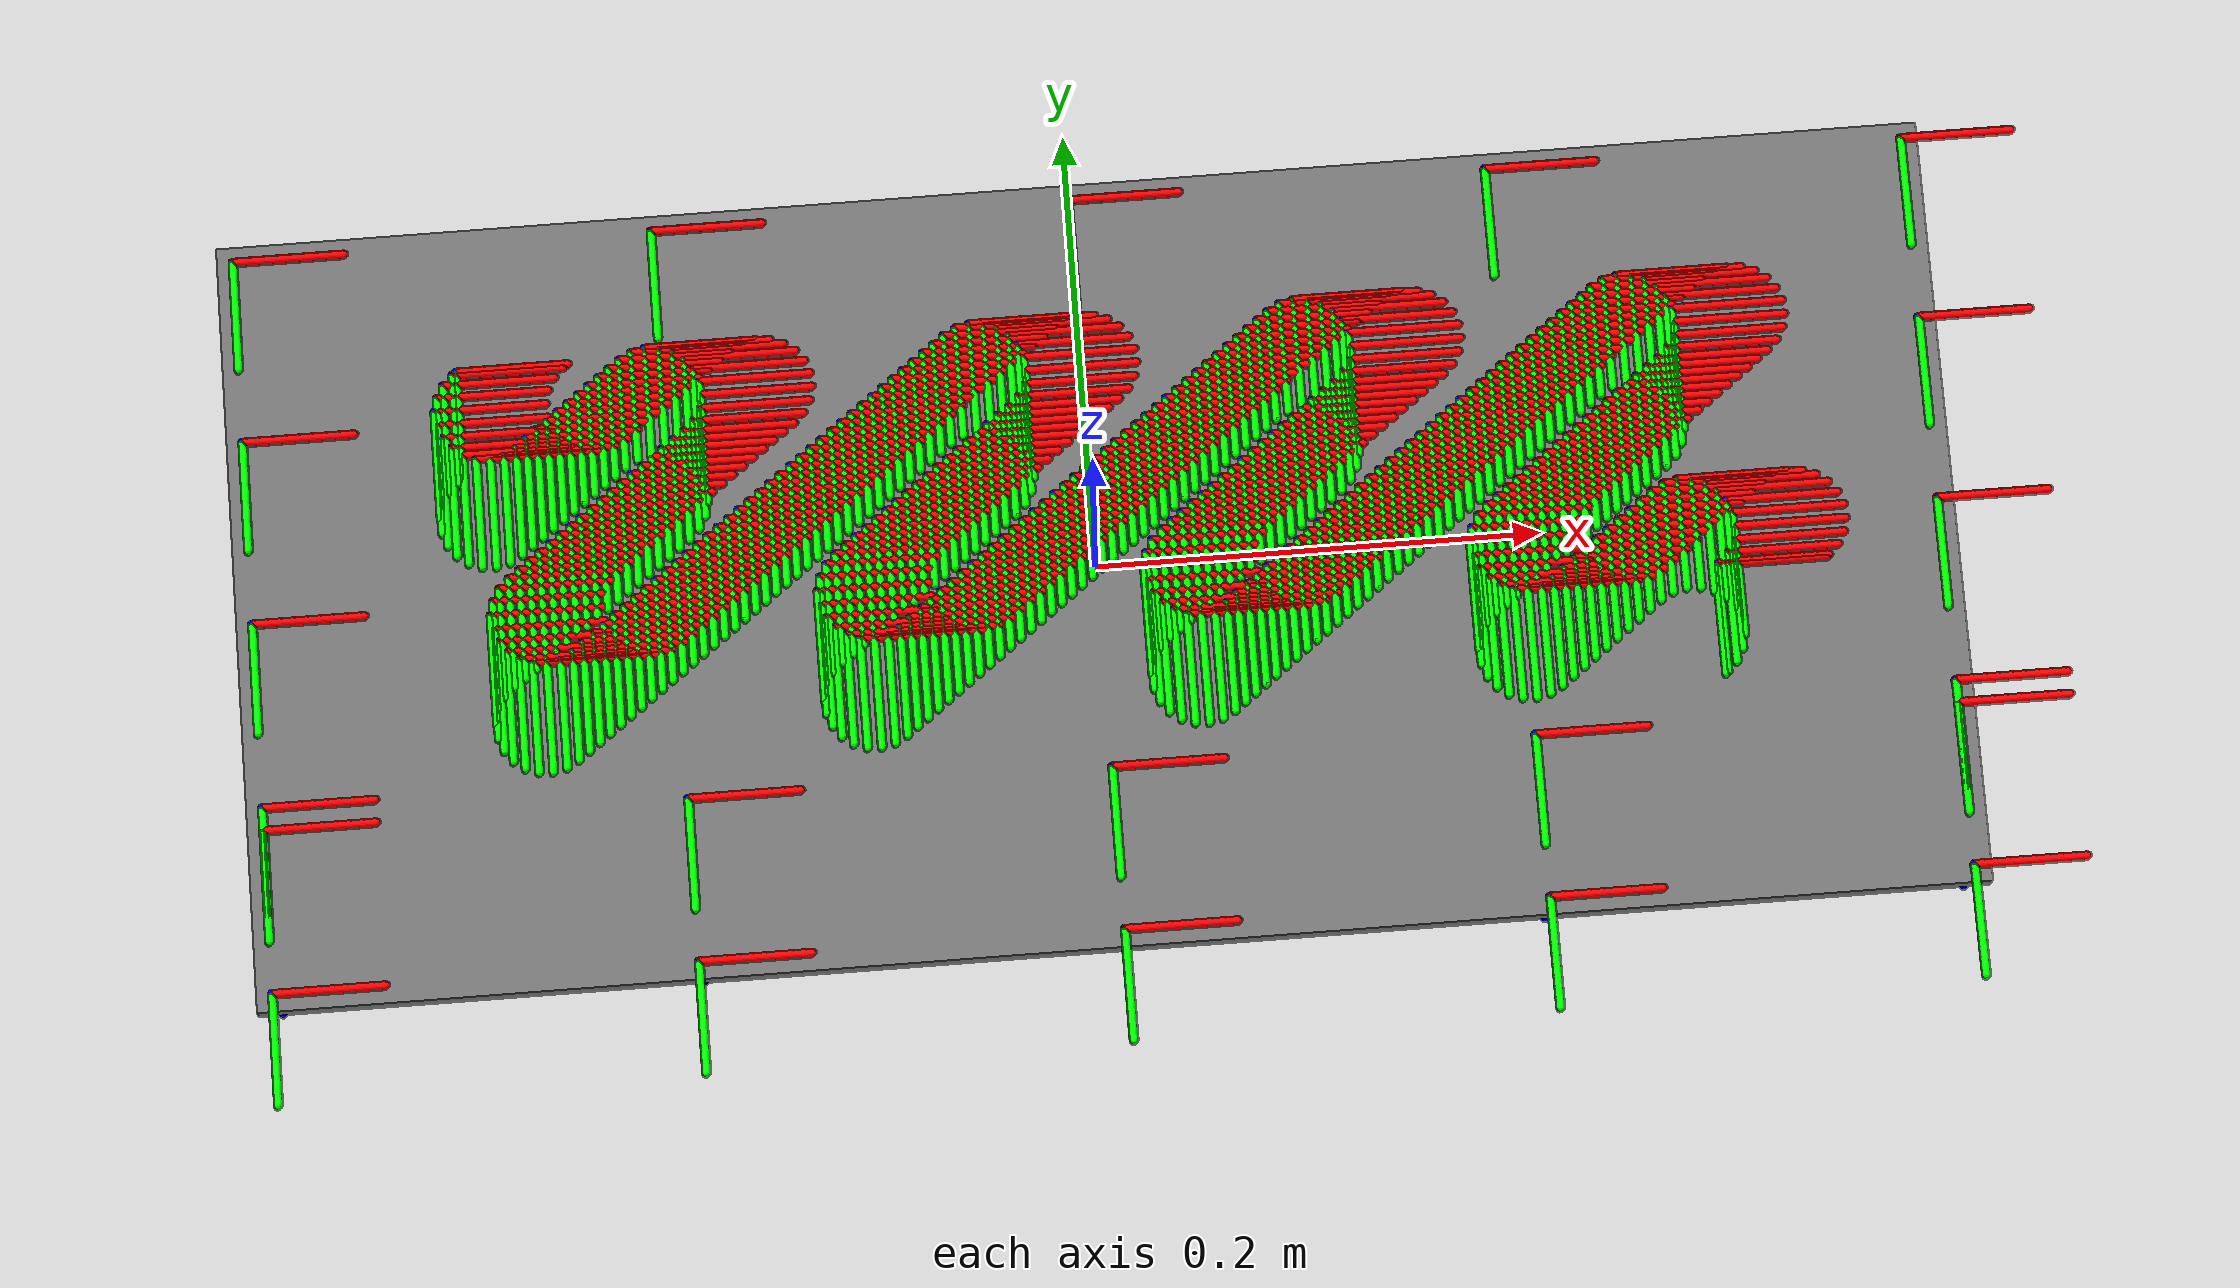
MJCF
<mujoco model="svin000412">
  <compiler angle="radian"/>
  <option timestep="0.01"/>

  <visual>
    <headlight diffuse="0.6 0.6 0.6" ambient="0.1 0.1 0.1" specular="0 0 0"/>
    <rgba haze="0.15 0.25 0.35 1"/>
    <global azimuth="120" elevation="-20"/>
  </visual>

  <asset>
    <mesh name="svin000412_mesh" file="svin000412.obj"/>
    <mesh name="svin000412_collision_mesh" file="svin000412.obj"/>
  </asset>

  <default>
    <geom condim="3" friction="1 0.5 0.01" solref="0.02 1" solimp="0.9 0.95 0.001"/>
  </default>

  <worldbody>
    <body name="svin000412" pos="0 0 0">

      <geom type="mesh" mesh="svin000412_mesh" rgba="0.45 0.45 0.45 1" contype="0" conaffinity="0" group="0"/>

      <!-- Collisions-->
      <geom name="svin000412_collision" type="mesh" mesh="svin000412_collision_mesh" pos="0 0 0" rgba="0.7 0.1 0.1 0.3" contype="1" conaffinity="1" group="3"/>

      <!-- center of the piece -->
      <site name="svin000412_site" pos="0.0 0.0 0.0" size="0.005" rgba="1 0 0 1"/>

      <!-- TRAJECTORY 1 -->

      <!-- Size A -->
      <body name="point_0_traj_1" pos="-0.377 0.1675 0.012" quat="0 1 0 0">
        <geom type="capsule" fromto="0 0 0 0.05 0 0" rgba="1 0 0 1" size="0.002" contype="0" conaffinity="0"/>
        <geom type="capsule" fromto="0 0 0 0 0.05 0" rgba="0 1 0 1" size="0.002" contype="0" conaffinity="0"/>
        <geom type="capsule" fromto="0 0 0 0 0 0.05" rgba="0 0 1 1" size="0.002" contype="0" conaffinity="0"/>
      </body>

      <body name="point_1_traj_1" pos="-0.1885 0.1675 0.012" quat="0 1 0 0">
        <geom type="capsule" fromto="0 0 0 0.05 0 0" rgba="1 0 0 1" size="0.002" contype="0" conaffinity="0"/>
        <geom type="capsule" fromto="0 0 0 0 0.05 0" rgba="0 1 0 1" size="0.002" contype="0" conaffinity="0"/>
        <geom type="capsule" fromto="0 0 0 0 0 0.05" rgba="0 0 1 1" size="0.002" contype="0" conaffinity="0"/>
      </body>

      <body name="point_2_traj_1" pos="0.0 0.1675 0.012" quat="0 1 0 0">
        <geom type="capsule" fromto="0 0 0 0.05 0 0" rgba="1 0 0 1" size="0.002" contype="0" conaffinity="0"/>
        <geom type="capsule" fromto="0 0 0 0 0.05 0" rgba="0 1 0 1" size="0.002" contype="0" conaffinity="0"/>
        <geom type="capsule" fromto="0 0 0 0 0 0.05" rgba="0 0 1 1" size="0.002" contype="0" conaffinity="0"/>
      </body>

      <body name="point_3_traj_1" pos="0.1885 0.1675 0.012" quat="0 1 0 0">
        <geom type="capsule" fromto="0 0 0 0.05 0 0" rgba="1 0 0 1" size="0.002" contype="0" conaffinity="0"/>
        <geom type="capsule" fromto="0 0 0 0 0.05 0" rgba="0 1 0 1" size="0.002" contype="0" conaffinity="0"/>
        <geom type="capsule" fromto="0 0 0 0 0 0.05" rgba="0 0 1 1" size="0.002" contype="0" conaffinity="0"/>
      </body>

      <body name="point_4_traj_1" pos="0.377 0.1675 0.012" quat="0 1 0 0">
        <geom type="capsule" fromto="0 0 0 0.05 0 0" rgba="1 0 0 1" size="0.002" contype="0" conaffinity="0"/>
        <geom type="capsule" fromto="0 0 0 0 0.05 0" rgba="0 1 0 1" size="0.002" contype="0" conaffinity="0"/>
        <geom type="capsule" fromto="0 0 0 0 0 0.05" rgba="0 0 1 1" size="0.002" contype="0" conaffinity="0"/>
      </body>

      <!-- Size B -->
      <body name="point_5_traj_1" pos="0.377 0.08375 0.012" quat="0 1 0 0">
        <geom type="capsule" fromto="0 0 0 0.05 0 0" rgba="1 0 0 1" size="0.002" contype="0" conaffinity="0"/>
        <geom type="capsule" fromto="0 0 0 0 0.05 0" rgba="0 1 0 1" size="0.002" contype="0" conaffinity="0"/>
        <geom type="capsule" fromto="0 0 0 0 0 0.05" rgba="0 0 1 1" size="0.002" contype="0" conaffinity="0"/>
      </body>

      <body name="point_6_traj_1" pos="0.377 0.0 0.012" quat="0 1 0 0">
        <geom type="capsule" fromto="0 0 0 0.05 0 0" rgba="1 0 0 1" size="0.002" contype="0" conaffinity="0"/>
        <geom type="capsule" fromto="0 0 0 0 0.05 0" rgba="0 1 0 1" size="0.002" contype="0" conaffinity="0"/>
        <geom type="capsule" fromto="0 0 0 0 0 0.05" rgba="0 0 1 1" size="0.002" contype="0" conaffinity="0"/>
      </body>

      <body name="point_7_traj_1" pos="0.377 -0.08375 0.012" quat="0 1 0 0">
        <geom type="capsule" fromto="0 0 0 0.05 0 0" rgba="1 0 0 1" size="0.002" contype="0" conaffinity="0"/>
        <geom type="capsule" fromto="0 0 0 0 0.05 0" rgba="0 1 0 1" size="0.002" contype="0" conaffinity="0"/>
        <geom type="capsule" fromto="0 0 0 0 0 0.05" rgba="0 0 1 1" size="0.002" contype="0" conaffinity="0"/>
      </body>

      <body name="point_8_traj_1" pos="0.377 -0.1675 0.012" quat="0 1 0 0">
        <geom type="capsule" fromto="0 0 0 0.05 0 0" rgba="1 0 0 1" size="0.002" contype="0" conaffinity="0"/>
        <geom type="capsule" fromto="0 0 0 0 0.05 0" rgba="0 1 0 1" size="0.002" contype="0" conaffinity="0"/>
        <geom type="capsule" fromto="0 0 0 0 0 0.05" rgba="0 0 1 1" size="0.002" contype="0" conaffinity="0"/>
      </body>

      <!-- Size C -->
      <body name="point_9_traj_1" pos="0.1885 -0.1675 0.012" quat="0 1 0 0">
        <geom type="capsule" fromto="0 0 0 0.05 0 0" rgba="1 0 0 1" size="0.002" contype="0" conaffinity="0"/>
        <geom type="capsule" fromto="0 0 0 0 0.05 0" rgba="0 1 0 1" size="0.002" contype="0" conaffinity="0"/>
        <geom type="capsule" fromto="0 0 0 0 0 0.05" rgba="0 0 1 1" size="0.002" contype="0" conaffinity="0"/>
      </body>

      <body name="point_10_traj_1" pos="0.0 -0.1675 0.012" quat="0 1 0 0">
        <geom type="capsule" fromto="0 0 0 0.05 0 0" rgba="1 0 0 1" size="0.002" contype="0" conaffinity="0"/>
        <geom type="capsule" fromto="0 0 0 0 0.05 0" rgba="0 1 0 1" size="0.002" contype="0" conaffinity="0"/>
        <geom type="capsule" fromto="0 0 0 0 0 0.05" rgba="0 0 1 1" size="0.002" contype="0" conaffinity="0"/>
      </body>

      <body name="point_11_traj_1" pos="-0.1885 -0.1675 0.012" quat="0 1 0 0">
        <geom type="capsule" fromto="0 0 0 0.05 0 0" rgba="1 0 0 1" size="0.002" contype="0" conaffinity="0"/>
        <geom type="capsule" fromto="0 0 0 0 0.05 0" rgba="0 1 0 1" size="0.002" contype="0" conaffinity="0"/>
        <geom type="capsule" fromto="0 0 0 0 0 0.05" rgba="0 0 1 1" size="0.002" contype="0" conaffinity="0"/>
      </body>

      <body name="point_12_traj_1" pos="-0.377 -0.1675 0.012" quat="0 1 0 0">
        <geom type="capsule" fromto="0 0 0 0.05 0 0" rgba="1 0 0 1" size="0.002" contype="0" conaffinity="0"/>
        <geom type="capsule" fromto="0 0 0 0 0.05 0" rgba="0 1 0 1" size="0.002" contype="0" conaffinity="0"/>
        <geom type="capsule" fromto="0 0 0 0 0 0.05" rgba="0 0 1 1" size="0.002" contype="0" conaffinity="0"/>
      </body>

      <!-- Size D -->
      <body name="point_13_traj_1" pos="-0.377 -0.08375 0.012" quat="0 1 0 0">
        <geom type="capsule" fromto="0 0 0 0.05 0 0" rgba="1 0 0 1" size="0.002" contype="0" conaffinity="0"/>
        <geom type="capsule" fromto="0 0 0 0 0.05 0" rgba="0 1 0 1" size="0.002" contype="0" conaffinity="0"/>
        <geom type="capsule" fromto="0 0 0 0 0 0.05" rgba="0 0 1 1" size="0.002" contype="0" conaffinity="0"/>
      </body>

      <body name="point_14_traj_1" pos="-0.377 0.0 0.012" quat="0 1 0 0">
        <geom type="capsule" fromto="0 0 0 0.05 0 0" rgba="1 0 0 1" size="0.002" contype="0" conaffinity="0"/>
        <geom type="capsule" fromto="0 0 0 0 0.05 0" rgba="0 1 0 1" size="0.002" contype="0" conaffinity="0"/>
        <geom type="capsule" fromto="0 0 0 0 0 0.05" rgba="0 0 1 1" size="0.002" contype="0" conaffinity="0"/>
      </body>

      <body name="point_15_traj_1" pos="-0.377 0.08375 0.012" quat="0 1 0 0">
        <geom type="capsule" fromto="0 0 0 0.05 0 0" rgba="1 0 0 1" size="0.002" contype="0" conaffinity="0"/>
        <geom type="capsule" fromto="0 0 0 0 0.05 0" rgba="0 1 0 1" size="0.002" contype="0" conaffinity="0"/>
        <geom type="capsule" fromto="0 0 0 0 0 0.05" rgba="0 0 1 1" size="0.002" contype="0" conaffinity="0"/>
      </body>

      <body name="point_16_traj_1" pos="-0.377 0.1675 0.012" quat="0 1 0 0">
        <geom type="capsule" fromto="0 0 0 0.05 0 0" rgba="1 0 0 1" size="0.002" contype="0" conaffinity="0"/>
        <geom type="capsule" fromto="0 0 0 0 0.05 0" rgba="0 1 0 1" size="0.002" contype="0" conaffinity="0"/>
        <geom type="capsule" fromto="0 0 0 0 0 0.05" rgba="0 0 1 1" size="0.002" contype="0" conaffinity="0"/>
      </body>

      <!-- TRAJECTORY 2 -->

      <body name="point_0_traj_2" pos="-0.377 -0.094 0.012" quat="0 1 0 0">
        <geom type="capsule" fromto="0 0 0 0.05 0 0" rgba="1 0 0 1" size="0.002" contype="0" conaffinity="0"/>
        <geom type="capsule" fromto="0 0 0 0 0.05 0" rgba="0 1 0 1" size="0.002" contype="0" conaffinity="0"/>
        <geom type="capsule" fromto="0 0 0 0 0 0.05" rgba="0 0 1 1" size="0.002" contype="0" conaffinity="0"/>
      </body>

      <body name="point_1_traj_2" pos="-0.1885 -0.094 0.012" quat="0 1 0 0">
        <geom type="capsule" fromto="0 0 0 0.05 0 0" rgba="1 0 0 1" size="0.002" contype="0" conaffinity="0"/>
        <geom type="capsule" fromto="0 0 0 0 0.05 0" rgba="0 1 0 1" size="0.002" contype="0" conaffinity="0"/>
        <geom type="capsule" fromto="0 0 0 0 0 0.05" rgba="0 0 1 1" size="0.002" contype="0" conaffinity="0"/>
      </body>

      <body name="point_2_traj_2" pos="0.0 -0.094 0.012" quat="0 1 0 0">
        <geom type="capsule" fromto="0 0 0 0.05 0 0" rgba="1 0 0 1" size="0.002" contype="0" conaffinity="0"/>
        <geom type="capsule" fromto="0 0 0 0 0.05 0" rgba="0 1 0 1" size="0.002" contype="0" conaffinity="0"/>
        <geom type="capsule" fromto="0 0 0 0 0 0.05" rgba="0 0 1 1" size="0.002" contype="0" conaffinity="0"/>
      </body>

      <body name="point_3_traj_2" pos="0.1885 -0.094 0.012" quat="0 1 0 0">
        <geom type="capsule" fromto="0 0 0 0.05 0 0" rgba="1 0 0 1" size="0.002" contype="0" conaffinity="0"/>
        <geom type="capsule" fromto="0 0 0 0 0.05 0" rgba="0 1 0 1" size="0.002" contype="0" conaffinity="0"/>
        <geom type="capsule" fromto="0 0 0 0 0 0.05" rgba="0 0 1 1" size="0.002" contype="0" conaffinity="0"/>
      </body>

      <body name="point_4_traj_2" pos="0.377 -0.094 0.012" quat="0 1 0 0">
        <geom type="capsule" fromto="0 0 0 0.05 0 0" rgba="1 0 0 1" size="0.002" contype="0" conaffinity="0"/>
        <geom type="capsule" fromto="0 0 0 0 0.05 0" rgba="0 1 0 1" size="0.002" contype="0" conaffinity="0"/>
        <geom type="capsule" fromto="0 0 0 0 0 0.05" rgba="0 0 1 1" size="0.002" contype="0" conaffinity="0"/>
      </body>

      <!-- TRAJECTORY 3 -->

      <body name="point_0_traj_3" pos="-0.279645 0.108740 0.012" quat="0 1 0 0">
        <geom type="capsule" fromto="0 0 0 0.05 0 0" rgba="1 0 0 1" size="0.002" contype="0" conaffinity="0"/>
        <geom type="capsule" fromto="0 0 0 0 0.05 0" rgba="0 1 0 1" size="0.002" contype="0" conaffinity="0"/>
        <geom type="capsule" fromto="0 0 0 0 0 0.05" rgba="0 0 1 1" size="0.002" contype="0" conaffinity="0"/>
      </body>

      <body name="point_1_traj_3" pos="-0.281460 0.107375 0.012" quat="0 1 0 0">
        <geom type="capsule" fromto="0 0 0 0.05 0 0" rgba="1 0 0 1" size="0.002" contype="0" conaffinity="0"/>
        <geom type="capsule" fromto="0 0 0 0 0.05 0" rgba="0 1 0 1" size="0.002" contype="0" conaffinity="0"/>
        <geom type="capsule" fromto="0 0 0 0 0 0.05" rgba="0 0 1 1" size="0.002" contype="0" conaffinity="0"/>
      </body>

      <body name="point_2_traj_3" pos="-0.285990 0.102845 0.012" quat="0 1 0 0">
        <geom type="capsule" fromto="0 0 0 0.05 0 0" rgba="1 0 0 1" size="0.002" contype="0" conaffinity="0"/>
        <geom type="capsule" fromto="0 0 0 0 0.05 0" rgba="0 1 0 1" size="0.002" contype="0" conaffinity="0"/>
        <geom type="capsule" fromto="0 0 0 0 0 0.05" rgba="0 0 1 1" size="0.002" contype="0" conaffinity="0"/>
      </body>

      <body name="point_3_traj_3" pos="-0.289080 0.097265 0.012" quat="0 1 0 0">
        <geom type="capsule" fromto="0 0 0 0.05 0 0" rgba="1 0 0 1" size="0.002" contype="0" conaffinity="0"/>
        <geom type="capsule" fromto="0 0 0 0 0.05 0" rgba="0 1 0 1" size="0.002" contype="0" conaffinity="0"/>
        <geom type="capsule" fromto="0 0 0 0 0 0.05" rgba="0 0 1 1" size="0.002" contype="0" conaffinity="0"/>
      </body>

      <body name="point_4_traj_3" pos="-0.290475 0.091085 0.012" quat="0 1 0 0">
        <geom type="capsule" fromto="0 0 0 0.05 0 0" rgba="1 0 0 1" size="0.002" contype="0" conaffinity="0"/>
        <geom type="capsule" fromto="0 0 0 0 0.05 0" rgba="0 1 0 1" size="0.002" contype="0" conaffinity="0"/>
        <geom type="capsule" fromto="0 0 0 0 0 0.05" rgba="0 0 1 1" size="0.002" contype="0" conaffinity="0"/>
      </body>

      <body name="point_5_traj_3" pos="-0.290070 0.084800 0.012" quat="0 1 0 0">
        <geom type="capsule" fromto="0 0 0 0.05 0 0" rgba="1 0 0 1" size="0.002" contype="0" conaffinity="0"/>
        <geom type="capsule" fromto="0 0 0 0 0.05 0" rgba="0 1 0 1" size="0.002" contype="0" conaffinity="0"/>
        <geom type="capsule" fromto="0 0 0 0 0 0.05" rgba="0 0 1 1" size="0.002" contype="0" conaffinity="0"/>
      </body>

      <body name="point_6_traj_3" pos="-0.287910 0.078920 0.012" quat="0 1 0 0">
        <geom type="capsule" fromto="0 0 0 0.05 0 0" rgba="1 0 0 1" size="0.002" contype="0" conaffinity="0"/>
        <geom type="capsule" fromto="0 0 0 0 0.05 0" rgba="0 1 0 1" size="0.002" contype="0" conaffinity="0"/>
        <geom type="capsule" fromto="0 0 0 0 0 0.05" rgba="0 0 1 1" size="0.002" contype="0" conaffinity="0"/>
      </body>

      <body name="point_7_traj_3" pos="-0.284145 0.073925 0.012" quat="0 1 0 0">
        <geom type="capsule" fromto="0 0 0 0.05 0 0" rgba="1 0 0 1" size="0.002" contype="0" conaffinity="0"/>
        <geom type="capsule" fromto="0 0 0 0 0.05 0" rgba="0 1 0 1" size="0.002" contype="0" conaffinity="0"/>
        <geom type="capsule" fromto="0 0 0 0 0 0.05" rgba="0 0 1 1" size="0.002" contype="0" conaffinity="0"/>
      </body>

      <body name="point_8_traj_3" pos="-0.279090 0.070220 0.012" quat="0 1 0 0">
        <geom type="capsule" fromto="0 0 0 0.05 0 0" rgba="1 0 0 1" size="0.002" contype="0" conaffinity="0"/>
        <geom type="capsule" fromto="0 0 0 0 0.05 0" rgba="0 1 0 1" size="0.002" contype="0" conaffinity="0"/>
        <geom type="capsule" fromto="0 0 0 0 0 0.05" rgba="0 0 1 1" size="0.002" contype="0" conaffinity="0"/>
      </body>

      <body name="point_9_traj_3" pos="-0.273165 0.068105 0.012" quat="0 1 0 0">
        <geom type="capsule" fromto="0 0 0 0.05 0 0" rgba="1 0 0 1" size="0.002" contype="0" conaffinity="0"/>
        <geom type="capsule" fromto="0 0 0 0 0.05 0" rgba="0 1 0 1" size="0.002" contype="0" conaffinity="0"/>
        <geom type="capsule" fromto="0 0 0 0 0 0.05" rgba="0 0 1 1" size="0.002" contype="0" conaffinity="0"/>
      </body>

      <body name="point_10_traj_3" pos="-0.266835 0.067745 0.012" quat="0 1 0 0">
        <geom type="capsule" fromto="0 0 0 0.05 0 0" rgba="1 0 0 1" size="0.002" contype="0" conaffinity="0"/>
        <geom type="capsule" fromto="0 0 0 0 0.05 0" rgba="0 1 0 1" size="0.002" contype="0" conaffinity="0"/>
        <geom type="capsule" fromto="0 0 0 0 0 0.05" rgba="0 0 1 1" size="0.002" contype="0" conaffinity="0"/>
      </body>

      <body name="point_11_traj_3" pos="-0.260610 0.069185 0.012" quat="0 1 0 0">
        <geom type="capsule" fromto="0 0 0 0.05 0 0" rgba="1 0 0 1" size="0.002" contype="0" conaffinity="0"/>
        <geom type="capsule" fromto="0 0 0 0 0.05 0" rgba="0 1 0 1" size="0.002" contype="0" conaffinity="0"/>
        <geom type="capsule" fromto="0 0 0 0 0 0.05" rgba="0 0 1 1" size="0.002" contype="0" conaffinity="0"/>
      </body>

      <body name="point_12_traj_3" pos="-0.255015 0.072290 0.012" quat="0 1 0 0">
        <geom type="capsule" fromto="0 0 0 0.05 0 0" rgba="1 0 0 1" size="0.002" contype="0" conaffinity="0"/>
        <geom type="capsule" fromto="0 0 0 0 0.05 0" rgba="0 1 0 1" size="0.002" contype="0" conaffinity="0"/>
        <geom type="capsule" fromto="0 0 0 0 0 0.05" rgba="0 0 1 1" size="0.002" contype="0" conaffinity="0"/>
      </body>

      <body name="point_13_traj_3" pos="-0.250185 0.075935 0.012" quat="0 1 0 0">
        <geom type="capsule" fromto="0 0 0 0.05 0 0" rgba="1 0 0 1" size="0.002" contype="0" conaffinity="0"/>
        <geom type="capsule" fromto="0 0 0 0 0.05 0" rgba="0 1 0 1" size="0.002" contype="0" conaffinity="0"/>
        <geom type="capsule" fromto="0 0 0 0 0 0.05" rgba="0 0 1 1" size="0.002" contype="0" conaffinity="0"/>
      </body>

      <body name="point_14_traj_3" pos="-0.245340 0.079580 0.012" quat="0 1 0 0">
        <geom type="capsule" fromto="0 0 0 0.05 0 0" rgba="1 0 0 1" size="0.002" contype="0" conaffinity="0"/>
        <geom type="capsule" fromto="0 0 0 0 0.05 0" rgba="0 1 0 1" size="0.002" contype="0" conaffinity="0"/>
        <geom type="capsule" fromto="0 0 0 0 0 0.05" rgba="0 0 1 1" size="0.002" contype="0" conaffinity="0"/>
      </body>

      <body name="point_15_traj_3" pos="-0.240510 0.083225 0.012" quat="0 1 0 0">
        <geom type="capsule" fromto="0 0 0 0.05 0 0" rgba="1 0 0 1" size="0.002" contype="0" conaffinity="0"/>
        <geom type="capsule" fromto="0 0 0 0 0.05 0" rgba="0 1 0 1" size="0.002" contype="0" conaffinity="0"/>
        <geom type="capsule" fromto="0 0 0 0 0 0.05" rgba="0 0 1 1" size="0.002" contype="0" conaffinity="0"/>
      </body>

      <body name="point_16_traj_3" pos="-0.235665 0.086870 0.012" quat="0 1 0 0">
        <geom type="capsule" fromto="0 0 0 0.05 0 0" rgba="1 0 0 1" size="0.002" contype="0" conaffinity="0"/>
        <geom type="capsule" fromto="0 0 0 0 0.05 0" rgba="0 1 0 1" size="0.002" contype="0" conaffinity="0"/>
        <geom type="capsule" fromto="0 0 0 0 0 0.05" rgba="0 0 1 1" size="0.002" contype="0" conaffinity="0"/>
      </body>

      <body name="point_17_traj_3" pos="-0.230835 0.090515 0.012" quat="0 1 0 0">
        <geom type="capsule" fromto="0 0 0 0.05 0 0" rgba="1 0 0 1" size="0.002" contype="0" conaffinity="0"/>
        <geom type="capsule" fromto="0 0 0 0 0.05 0" rgba="0 1 0 1" size="0.002" contype="0" conaffinity="0"/>
        <geom type="capsule" fromto="0 0 0 0 0 0.05" rgba="0 0 1 1" size="0.002" contype="0" conaffinity="0"/>
      </body>

      <body name="point_18_traj_3" pos="-0.225990 0.094160 0.012" quat="0 1 0 0">
        <geom type="capsule" fromto="0 0 0 0.05 0 0" rgba="1 0 0 1" size="0.002" contype="0" conaffinity="0"/>
        <geom type="capsule" fromto="0 0 0 0 0.05 0" rgba="0 1 0 1" size="0.002" contype="0" conaffinity="0"/>
        <geom type="capsule" fromto="0 0 0 0 0 0.05" rgba="0 0 1 1" size="0.002" contype="0" conaffinity="0"/>
      </body>

      <body name="point_19_traj_3" pos="-0.221160 0.097805 0.012" quat="0 1 0 0">
        <geom type="capsule" fromto="0 0 0 0.05 0 0" rgba="1 0 0 1" size="0.002" contype="0" conaffinity="0"/>
        <geom type="capsule" fromto="0 0 0 0 0.05 0" rgba="0 1 0 1" size="0.002" contype="0" conaffinity="0"/>
        <geom type="capsule" fromto="0 0 0 0 0 0.05" rgba="0 0 1 1" size="0.002" contype="0" conaffinity="0"/>
      </body>

      <body name="point_20_traj_3" pos="-0.216315 0.101450 0.012" quat="0 1 0 0">
        <geom type="capsule" fromto="0 0 0 0.05 0 0" rgba="1 0 0 1" size="0.002" contype="0" conaffinity="0"/>
        <geom type="capsule" fromto="0 0 0 0 0.05 0" rgba="0 1 0 1" size="0.002" contype="0" conaffinity="0"/>
        <geom type="capsule" fromto="0 0 0 0 0 0.05" rgba="0 0 1 1" size="0.002" contype="0" conaffinity="0"/>
      </body>

      <body name="point_21_traj_3" pos="-0.211485 0.105095 0.012" quat="0 1 0 0">
        <geom type="capsule" fromto="0 0 0 0.05 0 0" rgba="1 0 0 1" size="0.002" contype="0" conaffinity="0"/>
        <geom type="capsule" fromto="0 0 0 0 0.05 0" rgba="0 1 0 1" size="0.002" contype="0" conaffinity="0"/>
        <geom type="capsule" fromto="0 0 0 0 0 0.05" rgba="0 0 1 1" size="0.002" contype="0" conaffinity="0"/>
      </body>

      <body name="point_22_traj_3" pos="-0.206640 0.108740 0.012" quat="0 1 0 0">
        <geom type="capsule" fromto="0 0 0 0.05 0 0" rgba="1 0 0 1" size="0.002" contype="0" conaffinity="0"/>
        <geom type="capsule" fromto="0 0 0 0 0.05 0" rgba="0 1 0 1" size="0.002" contype="0" conaffinity="0"/>
        <geom type="capsule" fromto="0 0 0 0 0 0.05" rgba="0 0 1 1" size="0.002" contype="0" conaffinity="0"/>
      </body>

      <body name="point_23_traj_3" pos="-0.201045 0.111845 0.012" quat="0 1 0 0">
        <geom type="capsule" fromto="0 0 0 0.05 0 0" rgba="1 0 0 1" size="0.002" contype="0" conaffinity="0"/>
        <geom type="capsule" fromto="0 0 0 0 0.05 0" rgba="0 1 0 1" size="0.002" contype="0" conaffinity="0"/>
        <geom type="capsule" fromto="0 0 0 0 0 0.05" rgba="0 0 1 1" size="0.002" contype="0" conaffinity="0"/>
      </body>

      <body name="point_24_traj_3" pos="-0.194835 0.113270 0.012" quat="0 1 0 0">
        <geom type="capsule" fromto="0 0 0 0.05 0 0" rgba="1 0 0 1" size="0.002" contype="0" conaffinity="0"/>
        <geom type="capsule" fromto="0 0 0 0 0.05 0" rgba="0 1 0 1" size="0.002" contype="0" conaffinity="0"/>
        <geom type="capsule" fromto="0 0 0 0 0 0.05" rgba="0 0 1 1" size="0.002" contype="0" conaffinity="0"/>
      </body>

      <body name="point_25_traj_3" pos="-0.188505 0.112925 0.012" quat="0 1 0 0">
        <geom type="capsule" fromto="0 0 0 0.05 0 0" rgba="1 0 0 1" size="0.002" contype="0" conaffinity="0"/>
        <geom type="capsule" fromto="0 0 0 0 0.05 0" rgba="0 1 0 1" size="0.002" contype="0" conaffinity="0"/>
        <geom type="capsule" fromto="0 0 0 0 0 0.05" rgba="0 0 1 1" size="0.002" contype="0" conaffinity="0"/>
      </body>

      <body name="point_26_traj_3" pos="-0.182565 0.110795 0.012" quat="0 1 0 0">
        <geom type="capsule" fromto="0 0 0 0.05 0 0" rgba="1 0 0 1" size="0.002" contype="0" conaffinity="0"/>
        <geom type="capsule" fromto="0 0 0 0 0.05 0" rgba="0 1 0 1" size="0.002" contype="0" conaffinity="0"/>
        <geom type="capsule" fromto="0 0 0 0 0 0.05" rgba="0 0 1 1" size="0.002" contype="0" conaffinity="0"/>
      </body>

      <body name="point_27_traj_3" pos="-0.177525 0.107090 0.012" quat="0 1 0 0">
        <geom type="capsule" fromto="0 0 0 0.05 0 0" rgba="1 0 0 1" size="0.002" contype="0" conaffinity="0"/>
        <geom type="capsule" fromto="0 0 0 0 0.05 0" rgba="0 1 0 1" size="0.002" contype="0" conaffinity="0"/>
        <geom type="capsule" fromto="0 0 0 0 0 0.05" rgba="0 0 1 1" size="0.002" contype="0" conaffinity="0"/>
      </body>

      <body name="point_28_traj_3" pos="-0.173760 0.102110 0.012" quat="0 1 0 0">
        <geom type="capsule" fromto="0 0 0 0.05 0 0" rgba="1 0 0 1" size="0.002" contype="0" conaffinity="0"/>
        <geom type="capsule" fromto="0 0 0 0 0.05 0" rgba="0 1 0 1" size="0.002" contype="0" conaffinity="0"/>
        <geom type="capsule" fromto="0 0 0 0 0 0.05" rgba="0 0 1 1" size="0.002" contype="0" conaffinity="0"/>
      </body>

      <body name="point_29_traj_3" pos="-0.171585 0.096230 0.012" quat="0 1 0 0">
        <geom type="capsule" fromto="0 0 0 0.05 0 0" rgba="1 0 0 1" size="0.002" contype="0" conaffinity="0"/>
        <geom type="capsule" fromto="0 0 0 0 0.05 0" rgba="0 1 0 1" size="0.002" contype="0" conaffinity="0"/>
        <geom type="capsule" fromto="0 0 0 0 0 0.05" rgba="0 0 1 1" size="0.002" contype="0" conaffinity="0"/>
      </body>

      <body name="point_30_traj_3" pos="-0.171180 0.089945 0.012" quat="0 1 0 0">
        <geom type="capsule" fromto="0 0 0 0.05 0 0" rgba="1 0 0 1" size="0.002" contype="0" conaffinity="0"/>
        <geom type="capsule" fromto="0 0 0 0 0.05 0" rgba="0 1 0 1" size="0.002" contype="0" conaffinity="0"/>
        <geom type="capsule" fromto="0 0 0 0 0 0.05" rgba="0 0 1 1" size="0.002" contype="0" conaffinity="0"/>
      </body>

      <body name="point_31_traj_3" pos="-0.172590 0.083765 0.012" quat="0 1 0 0">
        <geom type="capsule" fromto="0 0 0 0.05 0 0" rgba="1 0 0 1" size="0.002" contype="0" conaffinity="0"/>
        <geom type="capsule" fromto="0 0 0 0 0.05 0" rgba="0 1 0 1" size="0.002" contype="0" conaffinity="0"/>
        <geom type="capsule" fromto="0 0 0 0 0 0.05" rgba="0 0 1 1" size="0.002" contype="0" conaffinity="0"/>
      </body>

      <body name="point_32_traj_3" pos="-0.175680 0.078185 0.012" quat="0 1 0 0">
        <geom type="capsule" fromto="0 0 0 0.05 0 0" rgba="1 0 0 1" size="0.002" contype="0" conaffinity="0"/>
        <geom type="capsule" fromto="0 0 0 0 0.05 0" rgba="0 1 0 1" size="0.002" contype="0" conaffinity="0"/>
        <geom type="capsule" fromto="0 0 0 0 0 0.05" rgba="0 0 1 1" size="0.002" contype="0" conaffinity="0"/>
      </body>

      <body name="point_33_traj_3" pos="-0.180210 0.073655 0.012" quat="0 1 0 0">
        <geom type="capsule" fromto="0 0 0 0.05 0 0" rgba="1 0 0 1" size="0.002" contype="0" conaffinity="0"/>
        <geom type="capsule" fromto="0 0 0 0 0.05 0" rgba="0 1 0 1" size="0.002" contype="0" conaffinity="0"/>
        <geom type="capsule" fromto="0 0 0 0 0 0.05" rgba="0 0 1 1" size="0.002" contype="0" conaffinity="0"/>
      </body>

      <body name="point_34_traj_3" pos="-0.185010 0.070040 0.012" quat="0 1 0 0">
        <geom type="capsule" fromto="0 0 0 0.05 0 0" rgba="1 0 0 1" size="0.002" contype="0" conaffinity="0"/>
        <geom type="capsule" fromto="0 0 0 0 0.05 0" rgba="0 1 0 1" size="0.002" contype="0" conaffinity="0"/>
        <geom type="capsule" fromto="0 0 0 0 0 0.05" rgba="0 0 1 1" size="0.002" contype="0" conaffinity="0"/>
      </body>

      <body name="point_35_traj_3" pos="-0.189810 0.066410 0.012" quat="0 1 0 0">
        <geom type="capsule" fromto="0 0 0 0.05 0 0" rgba="1 0 0 1" size="0.002" contype="0" conaffinity="0"/>
        <geom type="capsule" fromto="0 0 0 0 0.05 0" rgba="0 1 0 1" size="0.002" contype="0" conaffinity="0"/>
        <geom type="capsule" fromto="0 0 0 0 0 0.05" rgba="0 0 1 1" size="0.002" contype="0" conaffinity="0"/>
      </body>

      <body name="point_36_traj_3" pos="-0.194625 0.062795 0.012" quat="0 1 0 0">
        <geom type="capsule" fromto="0 0 0 0.05 0 0" rgba="1 0 0 1" size="0.002" contype="0" conaffinity="0"/>
        <geom type="capsule" fromto="0 0 0 0 0.05 0" rgba="0 1 0 1" size="0.002" contype="0" conaffinity="0"/>
        <geom type="capsule" fromto="0 0 0 0 0 0.05" rgba="0 0 1 1" size="0.002" contype="0" conaffinity="0"/>
      </body>

      <body name="point_37_traj_3" pos="-0.199425 0.059165 0.012" quat="0 1 0 0">
        <geom type="capsule" fromto="0 0 0 0.05 0 0" rgba="1 0 0 1" size="0.002" contype="0" conaffinity="0"/>
        <geom type="capsule" fromto="0 0 0 0 0.05 0" rgba="0 1 0 1" size="0.002" contype="0" conaffinity="0"/>
        <geom type="capsule" fromto="0 0 0 0 0 0.05" rgba="0 0 1 1" size="0.002" contype="0" conaffinity="0"/>
      </body>

      <body name="point_38_traj_3" pos="-0.204225 0.055550 0.012" quat="0 1 0 0">
        <geom type="capsule" fromto="0 0 0 0.05 0 0" rgba="1 0 0 1" size="0.002" contype="0" conaffinity="0"/>
        <geom type="capsule" fromto="0 0 0 0 0.05 0" rgba="0 1 0 1" size="0.002" contype="0" conaffinity="0"/>
        <geom type="capsule" fromto="0 0 0 0 0 0.05" rgba="0 0 1 1" size="0.002" contype="0" conaffinity="0"/>
      </body>

      <body name="point_39_traj_3" pos="-0.209040 0.051935 0.012" quat="0 1 0 0">
        <geom type="capsule" fromto="0 0 0 0.05 0 0" rgba="1 0 0 1" size="0.002" contype="0" conaffinity="0"/>
        <geom type="capsule" fromto="0 0 0 0 0.05 0" rgba="0 1 0 1" size="0.002" contype="0" conaffinity="0"/>
        <geom type="capsule" fromto="0 0 0 0 0 0.05" rgba="0 0 1 1" size="0.002" contype="0" conaffinity="0"/>
      </body>

      <body name="point_40_traj_3" pos="-0.213840 0.048305 0.012" quat="0 1 0 0">
        <geom type="capsule" fromto="0 0 0 0.05 0 0" rgba="1 0 0 1" size="0.002" contype="0" conaffinity="0"/>
        <geom type="capsule" fromto="0 0 0 0 0.05 0" rgba="0 1 0 1" size="0.002" contype="0" conaffinity="0"/>
        <geom type="capsule" fromto="0 0 0 0 0 0.05" rgba="0 0 1 1" size="0.002" contype="0" conaffinity="0"/>
      </body>

      <body name="point_41_traj_3" pos="-0.218655 0.044690 0.012" quat="0 1 0 0">
        <geom type="capsule" fromto="0 0 0 0.05 0 0" rgba="1 0 0 1" size="0.002" contype="0" conaffinity="0"/>
        <geom type="capsule" fromto="0 0 0 0 0.05 0" rgba="0 1 0 1" size="0.002" contype="0" conaffinity="0"/>
        <geom type="capsule" fromto="0 0 0 0 0 0.05" rgba="0 0 1 1" size="0.002" contype="0" conaffinity="0"/>
      </body>

      <body name="point_42_traj_3" pos="-0.223455 0.041060 0.012" quat="0 1 0 0">
        <geom type="capsule" fromto="0 0 0 0.05 0 0" rgba="1 0 0 1" size="0.002" contype="0" conaffinity="0"/>
        <geom type="capsule" fromto="0 0 0 0 0.05 0" rgba="0 1 0 1" size="0.002" contype="0" conaffinity="0"/>
        <geom type="capsule" fromto="0 0 0 0 0 0.05" rgba="0 0 1 1" size="0.002" contype="0" conaffinity="0"/>
      </body>

      <body name="point_43_traj_3" pos="-0.228255 0.037445 0.012" quat="0 1 0 0">
        <geom type="capsule" fromto="0 0 0 0.05 0 0" rgba="1 0 0 1" size="0.002" contype="0" conaffinity="0"/>
        <geom type="capsule" fromto="0 0 0 0 0.05 0" rgba="0 1 0 1" size="0.002" contype="0" conaffinity="0"/>
        <geom type="capsule" fromto="0 0 0 0 0 0.05" rgba="0 0 1 1" size="0.002" contype="0" conaffinity="0"/>
      </body>

      <body name="point_44_traj_3" pos="-0.233070 0.033830 0.012" quat="0 1 0 0">
        <geom type="capsule" fromto="0 0 0 0.05 0 0" rgba="1 0 0 1" size="0.002" contype="0" conaffinity="0"/>
        <geom type="capsule" fromto="0 0 0 0 0.05 0" rgba="0 1 0 1" size="0.002" contype="0" conaffinity="0"/>
        <geom type="capsule" fromto="0 0 0 0 0 0.05" rgba="0 0 1 1" size="0.002" contype="0" conaffinity="0"/>
      </body>

      <body name="point_45_traj_3" pos="-0.237870 0.030200 0.012" quat="0 1 0 0">
        <geom type="capsule" fromto="0 0 0 0.05 0 0" rgba="1 0 0 1" size="0.002" contype="0" conaffinity="0"/>
        <geom type="capsule" fromto="0 0 0 0 0.05 0" rgba="0 1 0 1" size="0.002" contype="0" conaffinity="0"/>
        <geom type="capsule" fromto="0 0 0 0 0 0.05" rgba="0 0 1 1" size="0.002" contype="0" conaffinity="0"/>
      </body>

      <body name="point_46_traj_3" pos="-0.242670 0.026585 0.012" quat="0 1 0 0">
        <geom type="capsule" fromto="0 0 0 0.05 0 0" rgba="1 0 0 1" size="0.002" contype="0" conaffinity="0"/>
        <geom type="capsule" fromto="0 0 0 0 0.05 0" rgba="0 1 0 1" size="0.002" contype="0" conaffinity="0"/>
        <geom type="capsule" fromto="0 0 0 0 0 0.05" rgba="0 0 1 1" size="0.002" contype="0" conaffinity="0"/>
      </body>

      <body name="point_47_traj_3" pos="-0.247485 0.022955 0.012" quat="0 1 0 0">
        <geom type="capsule" fromto="0 0 0 0.05 0 0" rgba="1 0 0 1" size="0.002" contype="0" conaffinity="0"/>
        <geom type="capsule" fromto="0 0 0 0 0.05 0" rgba="0 1 0 1" size="0.002" contype="0" conaffinity="0"/>
        <geom type="capsule" fromto="0 0 0 0 0 0.05" rgba="0 0 1 1" size="0.002" contype="0" conaffinity="0"/>
      </body>

      <body name="point_48_traj_3" pos="-0.252285 0.019340 0.012" quat="0 1 0 0">
        <geom type="capsule" fromto="0 0 0 0.05 0 0" rgba="1 0 0 1" size="0.002" contype="0" conaffinity="0"/>
        <geom type="capsule" fromto="0 0 0 0 0.05 0" rgba="0 1 0 1" size="0.002" contype="0" conaffinity="0"/>
        <geom type="capsule" fromto="0 0 0 0 0 0.05" rgba="0 0 1 1" size="0.002" contype="0" conaffinity="0"/>
      </body>

      <body name="point_49_traj_3" pos="-0.257085 0.015710 0.012" quat="0 1 0 0">
        <geom type="capsule" fromto="0 0 0 0.05 0 0" rgba="1 0 0 1" size="0.002" contype="0" conaffinity="0"/>
        <geom type="capsule" fromto="0 0 0 0 0.05 0" rgba="0 1 0 1" size="0.002" contype="0" conaffinity="0"/>
        <geom type="capsule" fromto="0 0 0 0 0 0.05" rgba="0 0 1 1" size="0.002" contype="0" conaffinity="0"/>
      </body>

      <body name="point_50_traj_3" pos="-0.261900 0.012095 0.012" quat="0 1 0 0">
        <geom type="capsule" fromto="0 0 0 0.05 0 0" rgba="1 0 0 1" size="0.002" contype="0" conaffinity="0"/>
        <geom type="capsule" fromto="0 0 0 0 0.05 0" rgba="0 1 0 1" size="0.002" contype="0" conaffinity="0"/>
        <geom type="capsule" fromto="0 0 0 0 0 0.05" rgba="0 0 1 1" size="0.002" contype="0" conaffinity="0"/>
      </body>

      <body name="point_51_traj_3" pos="-0.266430 0.007565 0.012" quat="0 1 0 0">
        <geom type="capsule" fromto="0 0 0 0.05 0 0" rgba="1 0 0 1" size="0.002" contype="0" conaffinity="0"/>
        <geom type="capsule" fromto="0 0 0 0 0.05 0" rgba="0 1 0 1" size="0.002" contype="0" conaffinity="0"/>
        <geom type="capsule" fromto="0 0 0 0 0 0.05" rgba="0 0 1 1" size="0.002" contype="0" conaffinity="0"/>
      </body>

      <body name="point_52_traj_3" pos="-0.269520 0.001985 0.012" quat="0 1 0 0">
        <geom type="capsule" fromto="0 0 0 0.05 0 0" rgba="1 0 0 1" size="0.002" contype="0" conaffinity="0"/>
        <geom type="capsule" fromto="0 0 0 0 0.05 0" rgba="0 1 0 1" size="0.002" contype="0" conaffinity="0"/>
        <geom type="capsule" fromto="0 0 0 0 0 0.05" rgba="0 0 1 1" size="0.002" contype="0" conaffinity="0"/>
      </body>

      <body name="point_53_traj_3" pos="-0.270915 -0.004195 0.012" quat="0 1 0 0">
        <geom type="capsule" fromto="0 0 0 0.05 0 0" rgba="1 0 0 1" size="0.002" contype="0" conaffinity="0"/>
        <geom type="capsule" fromto="0 0 0 0 0.05 0" rgba="0 1 0 1" size="0.002" contype="0" conaffinity="0"/>
        <geom type="capsule" fromto="0 0 0 0 0 0.05" rgba="0 0 1 1" size="0.002" contype="0" conaffinity="0"/>
      </body>

      <body name="point_54_traj_3" pos="-0.270510 -0.010480 0.012" quat="0 1 0 0">
        <geom type="capsule" fromto="0 0 0 0.05 0 0" rgba="1 0 0 1" size="0.002" contype="0" conaffinity="0"/>
        <geom type="capsule" fromto="0 0 0 0 0.05 0" rgba="0 1 0 1" size="0.002" contype="0" conaffinity="0"/>
        <geom type="capsule" fromto="0 0 0 0 0 0.05" rgba="0 0 1 1" size="0.002" contype="0" conaffinity="0"/>
      </body>

      <body name="point_55_traj_3" pos="-0.268350 -0.016345 0.012" quat="0 1 0 0">
        <geom type="capsule" fromto="0 0 0 0.05 0 0" rgba="1 0 0 1" size="0.002" contype="0" conaffinity="0"/>
        <geom type="capsule" fromto="0 0 0 0 0.05 0" rgba="0 1 0 1" size="0.002" contype="0" conaffinity="0"/>
        <geom type="capsule" fromto="0 0 0 0 0 0.05" rgba="0 0 1 1" size="0.002" contype="0" conaffinity="0"/>
      </body>

      <body name="point_56_traj_3" pos="-0.264585 -0.021340 0.012" quat="0 1 0 0">
        <geom type="capsule" fromto="0 0 0 0.05 0 0" rgba="1 0 0 1" size="0.002" contype="0" conaffinity="0"/>
        <geom type="capsule" fromto="0 0 0 0 0.05 0" rgba="0 1 0 1" size="0.002" contype="0" conaffinity="0"/>
        <geom type="capsule" fromto="0 0 0 0 0 0.05" rgba="0 0 1 1" size="0.002" contype="0" conaffinity="0"/>
      </body>

      <body name="point_57_traj_3" pos="-0.259530 -0.025045 0.012" quat="0 1 0 0">
        <geom type="capsule" fromto="0 0 0 0.05 0 0" rgba="1 0 0 1" size="0.002" contype="0" conaffinity="0"/>
        <geom type="capsule" fromto="0 0 0 0 0.05 0" rgba="0 1 0 1" size="0.002" contype="0" conaffinity="0"/>
        <geom type="capsule" fromto="0 0 0 0 0 0.05" rgba="0 0 1 1" size="0.002" contype="0" conaffinity="0"/>
      </body>

      <body name="point_58_traj_3" pos="-0.253605 -0.027160 0.012" quat="0 1 0 0">
        <geom type="capsule" fromto="0 0 0 0.05 0 0" rgba="1 0 0 1" size="0.002" contype="0" conaffinity="0"/>
        <geom type="capsule" fromto="0 0 0 0 0.05 0" rgba="0 1 0 1" size="0.002" contype="0" conaffinity="0"/>
        <geom type="capsule" fromto="0 0 0 0 0 0.05" rgba="0 0 1 1" size="0.002" contype="0" conaffinity="0"/>
      </body>

      <body name="point_59_traj_3" pos="-0.247275 -0.027520 0.012" quat="0 1 0 0">
        <geom type="capsule" fromto="0 0 0 0.05 0 0" rgba="1 0 0 1" size="0.002" contype="0" conaffinity="0"/>
        <geom type="capsule" fromto="0 0 0 0 0.05 0" rgba="0 1 0 1" size="0.002" contype="0" conaffinity="0"/>
        <geom type="capsule" fromto="0 0 0 0 0 0.05" rgba="0 0 1 1" size="0.002" contype="0" conaffinity="0"/>
      </body>

      <body name="point_60_traj_3" pos="-0.241050 -0.026095 0.012" quat="0 1 0 0">
        <geom type="capsule" fromto="0 0 0 0.05 0 0" rgba="1 0 0 1" size="0.002" contype="0" conaffinity="0"/>
        <geom type="capsule" fromto="0 0 0 0 0.05 0" rgba="0 1 0 1" size="0.002" contype="0" conaffinity="0"/>
        <geom type="capsule" fromto="0 0 0 0 0 0.05" rgba="0 0 1 1" size="0.002" contype="0" conaffinity="0"/>
      </body>

      <body name="point_61_traj_3" pos="-0.235455 -0.022990 0.012" quat="0 1 0 0">
        <geom type="capsule" fromto="0 0 0 0.05 0 0" rgba="1 0 0 1" size="0.002" contype="0" conaffinity="0"/>
        <geom type="capsule" fromto="0 0 0 0 0.05 0" rgba="0 1 0 1" size="0.002" contype="0" conaffinity="0"/>
        <geom type="capsule" fromto="0 0 0 0 0 0.05" rgba="0 0 1 1" size="0.002" contype="0" conaffinity="0"/>
      </body>

      <body name="point_62_traj_3" pos="-0.230610 -0.019330 0.012" quat="0 1 0 0">
        <geom type="capsule" fromto="0 0 0 0.05 0 0" rgba="1 0 0 1" size="0.002" contype="0" conaffinity="0"/>
        <geom type="capsule" fromto="0 0 0 0 0.05 0" rgba="0 1 0 1" size="0.002" contype="0" conaffinity="0"/>
        <geom type="capsule" fromto="0 0 0 0 0 0.05" rgba="0 0 1 1" size="0.002" contype="0" conaffinity="0"/>
      </body>

      <body name="point_63_traj_3" pos="-0.225750 -0.015670 0.012" quat="0 1 0 0">
        <geom type="capsule" fromto="0 0 0 0.05 0 0" rgba="1 0 0 1" size="0.002" contype="0" conaffinity="0"/>
        <geom type="capsule" fromto="0 0 0 0 0.05 0" rgba="0 1 0 1" size="0.002" contype="0" conaffinity="0"/>
        <geom type="capsule" fromto="0 0 0 0 0 0.05" rgba="0 0 1 1" size="0.002" contype="0" conaffinity="0"/>
      </body>

      <body name="point_64_traj_3" pos="-0.220890 -0.012010 0.012" quat="0 1 0 0">
        <geom type="capsule" fromto="0 0 0 0.05 0 0" rgba="1 0 0 1" size="0.002" contype="0" conaffinity="0"/>
        <geom type="capsule" fromto="0 0 0 0 0.05 0" rgba="0 1 0 1" size="0.002" contype="0" conaffinity="0"/>
        <geom type="capsule" fromto="0 0 0 0 0 0.05" rgba="0 0 1 1" size="0.002" contype="0" conaffinity="0"/>
      </body>

      <body name="point_65_traj_3" pos="-0.216030 -0.008350 0.012" quat="0 1 0 0">
        <geom type="capsule" fromto="0 0 0 0.05 0 0" rgba="1 0 0 1" size="0.002" contype="0" conaffinity="0"/>
        <geom type="capsule" fromto="0 0 0 0 0.05 0" rgba="0 1 0 1" size="0.002" contype="0" conaffinity="0"/>
        <geom type="capsule" fromto="0 0 0 0 0 0.05" rgba="0 0 1 1" size="0.002" contype="0" conaffinity="0"/>
      </body>

      <body name="point_66_traj_3" pos="-0.211185 -0.004690 0.012" quat="0 1 0 0">
        <geom type="capsule" fromto="0 0 0 0.05 0 0" rgba="1 0 0 1" size="0.002" contype="0" conaffinity="0"/>
        <geom type="capsule" fromto="0 0 0 0 0.05 0" rgba="0 1 0 1" size="0.002" contype="0" conaffinity="0"/>
        <geom type="capsule" fromto="0 0 0 0 0 0.05" rgba="0 0 1 1" size="0.002" contype="0" conaffinity="0"/>
      </body>

      <body name="point_67_traj_3" pos="-0.206325 -0.001030 0.012" quat="0 1 0 0">
        <geom type="capsule" fromto="0 0 0 0.05 0 0" rgba="1 0 0 1" size="0.002" contype="0" conaffinity="0"/>
        <geom type="capsule" fromto="0 0 0 0 0.05 0" rgba="0 1 0 1" size="0.002" contype="0" conaffinity="0"/>
        <geom type="capsule" fromto="0 0 0 0 0 0.05" rgba="0 0 1 1" size="0.002" contype="0" conaffinity="0"/>
      </body>

      <body name="point_68_traj_3" pos="-0.201465 0.002630 0.012" quat="0 1 0 0">
        <geom type="capsule" fromto="0 0 0 0.05 0 0" rgba="1 0 0 1" size="0.002" contype="0" conaffinity="0"/>
        <geom type="capsule" fromto="0 0 0 0 0.05 0" rgba="0 1 0 1" size="0.002" contype="0" conaffinity="0"/>
        <geom type="capsule" fromto="0 0 0 0 0 0.05" rgba="0 0 1 1" size="0.002" contype="0" conaffinity="0"/>
      </body>

      <body name="point_69_traj_3" pos="-0.196605 0.006290 0.012" quat="0 1 0 0">
        <geom type="capsule" fromto="0 0 0 0.05 0 0" rgba="1 0 0 1" size="0.002" contype="0" conaffinity="0"/>
        <geom type="capsule" fromto="0 0 0 0 0.05 0" rgba="0 1 0 1" size="0.002" contype="0" conaffinity="0"/>
        <geom type="capsule" fromto="0 0 0 0 0 0.05" rgba="0 0 1 1" size="0.002" contype="0" conaffinity="0"/>
      </body>

      <body name="point_70_traj_3" pos="-0.191760 0.009950 0.012" quat="0 1 0 0">
        <geom type="capsule" fromto="0 0 0 0.05 0 0" rgba="1 0 0 1" size="0.002" contype="0" conaffinity="0"/>
        <geom type="capsule" fromto="0 0 0 0 0.05 0" rgba="0 1 0 1" size="0.002" contype="0" conaffinity="0"/>
        <geom type="capsule" fromto="0 0 0 0 0 0.05" rgba="0 0 1 1" size="0.002" contype="0" conaffinity="0"/>
      </body>

      <body name="point_71_traj_3" pos="-0.186900 0.013610 0.012" quat="0 1 0 0">
        <geom type="capsule" fromto="0 0 0 0.05 0 0" rgba="1 0 0 1" size="0.002" contype="0" conaffinity="0"/>
        <geom type="capsule" fromto="0 0 0 0 0.05 0" rgba="0 1 0 1" size="0.002" contype="0" conaffinity="0"/>
        <geom type="capsule" fromto="0 0 0 0 0 0.05" rgba="0 0 1 1" size="0.002" contype="0" conaffinity="0"/>
      </body>

      <body name="point_72_traj_3" pos="-0.182040 0.017255 0.012" quat="0 1 0 0">
        <geom type="capsule" fromto="0 0 0 0.05 0 0" rgba="1 0 0 1" size="0.002" contype="0" conaffinity="0"/>
        <geom type="capsule" fromto="0 0 0 0 0.05 0" rgba="0 1 0 1" size="0.002" contype="0" conaffinity="0"/>
        <geom type="capsule" fromto="0 0 0 0 0 0.05" rgba="0 0 1 1" size="0.002" contype="0" conaffinity="0"/>
      </body>

      <body name="point_73_traj_3" pos="-0.177195 0.020915 0.012" quat="0 1 0 0">
        <geom type="capsule" fromto="0 0 0 0.05 0 0" rgba="1 0 0 1" size="0.002" contype="0" conaffinity="0"/>
        <geom type="capsule" fromto="0 0 0 0 0.05 0" rgba="0 1 0 1" size="0.002" contype="0" conaffinity="0"/>
        <geom type="capsule" fromto="0 0 0 0 0 0.05" rgba="0 0 1 1" size="0.002" contype="0" conaffinity="0"/>
      </body>

      <body name="point_74_traj_3" pos="-0.172335 0.024575 0.012" quat="0 1 0 0">
        <geom type="capsule" fromto="0 0 0 0.05 0 0" rgba="1 0 0 1" size="0.002" contype="0" conaffinity="0"/>
        <geom type="capsule" fromto="0 0 0 0 0.05 0" rgba="0 1 0 1" size="0.002" contype="0" conaffinity="0"/>
        <geom type="capsule" fromto="0 0 0 0 0 0.05" rgba="0 0 1 1" size="0.002" contype="0" conaffinity="0"/>
      </body>

      <body name="point_75_traj_3" pos="-0.167475 0.028235 0.012" quat="0 1 0 0">
        <geom type="capsule" fromto="0 0 0 0.05 0 0" rgba="1 0 0 1" size="0.002" contype="0" conaffinity="0"/>
        <geom type="capsule" fromto="0 0 0 0 0.05 0" rgba="0 1 0 1" size="0.002" contype="0" conaffinity="0"/>
        <geom type="capsule" fromto="0 0 0 0 0 0.05" rgba="0 0 1 1" size="0.002" contype="0" conaffinity="0"/>
      </body>

      <body name="point_76_traj_3" pos="-0.162615 0.031895 0.012" quat="0 1 0 0">
        <geom type="capsule" fromto="0 0 0 0.05 0 0" rgba="1 0 0 1" size="0.002" contype="0" conaffinity="0"/>
        <geom type="capsule" fromto="0 0 0 0 0.05 0" rgba="0 1 0 1" size="0.002" contype="0" conaffinity="0"/>
        <geom type="capsule" fromto="0 0 0 0 0 0.05" rgba="0 0 1 1" size="0.002" contype="0" conaffinity="0"/>
      </body>

      <body name="point_77_traj_3" pos="-0.157770 0.035555 0.012" quat="0 1 0 0">
        <geom type="capsule" fromto="0 0 0 0.05 0 0" rgba="1 0 0 1" size="0.002" contype="0" conaffinity="0"/>
        <geom type="capsule" fromto="0 0 0 0 0.05 0" rgba="0 1 0 1" size="0.002" contype="0" conaffinity="0"/>
        <geom type="capsule" fromto="0 0 0 0 0 0.05" rgba="0 0 1 1" size="0.002" contype="0" conaffinity="0"/>
      </body>

      <body name="point_78_traj_3" pos="-0.152910 0.039215 0.012" quat="0 1 0 0">
        <geom type="capsule" fromto="0 0 0 0.05 0 0" rgba="1 0 0 1" size="0.002" contype="0" conaffinity="0"/>
        <geom type="capsule" fromto="0 0 0 0 0.05 0" rgba="0 1 0 1" size="0.002" contype="0" conaffinity="0"/>
        <geom type="capsule" fromto="0 0 0 0 0 0.05" rgba="0 0 1 1" size="0.002" contype="0" conaffinity="0"/>
      </body>

      <body name="point_79_traj_3" pos="-0.148050 0.042875 0.012" quat="0 1 0 0">
        <geom type="capsule" fromto="0 0 0 0.05 0 0" rgba="1 0 0 1" size="0.002" contype="0" conaffinity="0"/>
        <geom type="capsule" fromto="0 0 0 0 0.05 0" rgba="0 1 0 1" size="0.002" contype="0" conaffinity="0"/>
        <geom type="capsule" fromto="0 0 0 0 0 0.05" rgba="0 0 1 1" size="0.002" contype="0" conaffinity="0"/>
      </body>

      <body name="point_80_traj_3" pos="-0.143205 0.046535 0.012" quat="0 1 0 0">
        <geom type="capsule" fromto="0 0 0 0.05 0 0" rgba="1 0 0 1" size="0.002" contype="0" conaffinity="0"/>
        <geom type="capsule" fromto="0 0 0 0 0.05 0" rgba="0 1 0 1" size="0.002" contype="0" conaffinity="0"/>
        <geom type="capsule" fromto="0 0 0 0 0 0.05" rgba="0 0 1 1" size="0.002" contype="0" conaffinity="0"/>
      </body>

      <body name="point_81_traj_3" pos="-0.138345 0.050195 0.012" quat="0 1 0 0">
        <geom type="capsule" fromto="0 0 0 0.05 0 0" rgba="1 0 0 1" size="0.002" contype="0" conaffinity="0"/>
        <geom type="capsule" fromto="0 0 0 0 0.05 0" rgba="0 1 0 1" size="0.002" contype="0" conaffinity="0"/>
        <geom type="capsule" fromto="0 0 0 0 0 0.05" rgba="0 0 1 1" size="0.002" contype="0" conaffinity="0"/>
      </body>

      <body name="point_82_traj_3" pos="-0.133485 0.053855 0.012" quat="0 1 0 0">
        <geom type="capsule" fromto="0 0 0 0.05 0 0" rgba="1 0 0 1" size="0.002" contype="0" conaffinity="0"/>
        <geom type="capsule" fromto="0 0 0 0 0.05 0" rgba="0 1 0 1" size="0.002" contype="0" conaffinity="0"/>
        <geom type="capsule" fromto="0 0 0 0 0 0.05" rgba="0 0 1 1" size="0.002" contype="0" conaffinity="0"/>
      </body>

      <body name="point_83_traj_3" pos="-0.128625 0.057515 0.012" quat="0 1 0 0">
        <geom type="capsule" fromto="0 0 0 0.05 0 0" rgba="1 0 0 1" size="0.002" contype="0" conaffinity="0"/>
        <geom type="capsule" fromto="0 0 0 0 0.05 0" rgba="0 1 0 1" size="0.002" contype="0" conaffinity="0"/>
        <geom type="capsule" fromto="0 0 0 0 0 0.05" rgba="0 0 1 1" size="0.002" contype="0" conaffinity="0"/>
      </body>

      <body name="point_84_traj_3" pos="-0.123780 0.061175 0.012" quat="0 1 0 0">
        <geom type="capsule" fromto="0 0 0 0.05 0 0" rgba="1 0 0 1" size="0.002" contype="0" conaffinity="0"/>
        <geom type="capsule" fromto="0 0 0 0 0.05 0" rgba="0 1 0 1" size="0.002" contype="0" conaffinity="0"/>
        <geom type="capsule" fromto="0 0 0 0 0 0.05" rgba="0 0 1 1" size="0.002" contype="0" conaffinity="0"/>
      </body>

      <body name="point_85_traj_3" pos="-0.118920 0.064835 0.012" quat="0 1 0 0">
        <geom type="capsule" fromto="0 0 0 0.05 0 0" rgba="1 0 0 1" size="0.002" contype="0" conaffinity="0"/>
        <geom type="capsule" fromto="0 0 0 0 0.05 0" rgba="0 1 0 1" size="0.002" contype="0" conaffinity="0"/>
        <geom type="capsule" fromto="0 0 0 0 0 0.05" rgba="0 0 1 1" size="0.002" contype="0" conaffinity="0"/>
      </body>

      <body name="point_86_traj_3" pos="-0.114060 0.068495 0.012" quat="0 1 0 0">
        <geom type="capsule" fromto="0 0 0 0.05 0 0" rgba="1 0 0 1" size="0.002" contype="0" conaffinity="0"/>
        <geom type="capsule" fromto="0 0 0 0 0.05 0" rgba="0 1 0 1" size="0.002" contype="0" conaffinity="0"/>
        <geom type="capsule" fromto="0 0 0 0 0 0.05" rgba="0 0 1 1" size="0.002" contype="0" conaffinity="0"/>
      </body>

      <body name="point_87_traj_3" pos="-0.109215 0.072155 0.012" quat="0 1 0 0">
        <geom type="capsule" fromto="0 0 0 0.05 0 0" rgba="1 0 0 1" size="0.002" contype="0" conaffinity="0"/>
        <geom type="capsule" fromto="0 0 0 0 0.05 0" rgba="0 1 0 1" size="0.002" contype="0" conaffinity="0"/>
        <geom type="capsule" fromto="0 0 0 0 0 0.05" rgba="0 0 1 1" size="0.002" contype="0" conaffinity="0"/>
      </body>

      <body name="point_88_traj_3" pos="-0.104355 0.075815 0.012" quat="0 1 0 0">
        <geom type="capsule" fromto="0 0 0 0.05 0 0" rgba="1 0 0 1" size="0.002" contype="0" conaffinity="0"/>
        <geom type="capsule" fromto="0 0 0 0 0.05 0" rgba="0 1 0 1" size="0.002" contype="0" conaffinity="0"/>
        <geom type="capsule" fromto="0 0 0 0 0 0.05" rgba="0 0 1 1" size="0.002" contype="0" conaffinity="0"/>
      </body>

      <body name="point_89_traj_3" pos="-0.099495 0.079460 0.012" quat="0 1 0 0">
        <geom type="capsule" fromto="0 0 0 0.05 0 0" rgba="1 0 0 1" size="0.002" contype="0" conaffinity="0"/>
        <geom type="capsule" fromto="0 0 0 0 0.05 0" rgba="0 1 0 1" size="0.002" contype="0" conaffinity="0"/>
        <geom type="capsule" fromto="0 0 0 0 0 0.05" rgba="0 0 1 1" size="0.002" contype="0" conaffinity="0"/>
      </body>

      <body name="point_90_traj_3" pos="-0.094635 0.083120 0.012" quat="0 1 0 0">
        <geom type="capsule" fromto="0 0 0 0.05 0 0" rgba="1 0 0 1" size="0.002" contype="0" conaffinity="0"/>
        <geom type="capsule" fromto="0 0 0 0 0.05 0" rgba="0 1 0 1" size="0.002" contype="0" conaffinity="0"/>
        <geom type="capsule" fromto="0 0 0 0 0 0.05" rgba="0 0 1 1" size="0.002" contype="0" conaffinity="0"/>
      </body>

      <body name="point_91_traj_3" pos="-0.089790 0.086780 0.012" quat="0 1 0 0">
        <geom type="capsule" fromto="0 0 0 0.05 0 0" rgba="1 0 0 1" size="0.002" contype="0" conaffinity="0"/>
        <geom type="capsule" fromto="0 0 0 0 0.05 0" rgba="0 1 0 1" size="0.002" contype="0" conaffinity="0"/>
        <geom type="capsule" fromto="0 0 0 0 0 0.05" rgba="0 0 1 1" size="0.002" contype="0" conaffinity="0"/>
      </body>

      <body name="point_92_traj_3" pos="-0.084930 0.090440 0.012" quat="0 1 0 0">
        <geom type="capsule" fromto="0 0 0 0.05 0 0" rgba="1 0 0 1" size="0.002" contype="0" conaffinity="0"/>
        <geom type="capsule" fromto="0 0 0 0 0.05 0" rgba="0 1 0 1" size="0.002" contype="0" conaffinity="0"/>
        <geom type="capsule" fromto="0 0 0 0 0 0.05" rgba="0 0 1 1" size="0.002" contype="0" conaffinity="0"/>
      </body>

      <body name="point_93_traj_3" pos="-0.080070 0.094100 0.012" quat="0 1 0 0">
        <geom type="capsule" fromto="0 0 0 0.05 0 0" rgba="1 0 0 1" size="0.002" contype="0" conaffinity="0"/>
        <geom type="capsule" fromto="0 0 0 0 0.05 0" rgba="0 1 0 1" size="0.002" contype="0" conaffinity="0"/>
        <geom type="capsule" fromto="0 0 0 0 0 0.05" rgba="0 0 1 1" size="0.002" contype="0" conaffinity="0"/>
      </body>

      <body name="point_94_traj_3" pos="-0.075225 0.097760 0.012" quat="0 1 0 0">
        <geom type="capsule" fromto="0 0 0 0.05 0 0" rgba="1 0 0 1" size="0.002" contype="0" conaffinity="0"/>
        <geom type="capsule" fromto="0 0 0 0 0.05 0" rgba="0 1 0 1" size="0.002" contype="0" conaffinity="0"/>
        <geom type="capsule" fromto="0 0 0 0 0 0.05" rgba="0 0 1 1" size="0.002" contype="0" conaffinity="0"/>
      </body>

      <body name="point_95_traj_3" pos="-0.070365 0.101420 0.012" quat="0 1 0 0">
        <geom type="capsule" fromto="0 0 0 0.05 0 0" rgba="1 0 0 1" size="0.002" contype="0" conaffinity="0"/>
        <geom type="capsule" fromto="0 0 0 0 0.05 0" rgba="0 1 0 1" size="0.002" contype="0" conaffinity="0"/>
        <geom type="capsule" fromto="0 0 0 0 0 0.05" rgba="0 0 1 1" size="0.002" contype="0" conaffinity="0"/>
      </body>

      <body name="point_96_traj_3" pos="-0.065505 0.105080 0.012" quat="0 1 0 0">
        <geom type="capsule" fromto="0 0 0 0.05 0 0" rgba="1 0 0 1" size="0.002" contype="0" conaffinity="0"/>
        <geom type="capsule" fromto="0 0 0 0 0.05 0" rgba="0 1 0 1" size="0.002" contype="0" conaffinity="0"/>
        <geom type="capsule" fromto="0 0 0 0 0 0.05" rgba="0 0 1 1" size="0.002" contype="0" conaffinity="0"/>
      </body>

      <body name="point_97_traj_3" pos="-0.060645 0.108740 0.012" quat="0 1 0 0">
        <geom type="capsule" fromto="0 0 0 0.05 0 0" rgba="1 0 0 1" size="0.002" contype="0" conaffinity="0"/>
        <geom type="capsule" fromto="0 0 0 0 0.05 0" rgba="0 1 0 1" size="0.002" contype="0" conaffinity="0"/>
        <geom type="capsule" fromto="0 0 0 0 0 0.05" rgba="0 0 1 1" size="0.002" contype="0" conaffinity="0"/>
      </body>

      <body name="point_98_traj_3" pos="-0.055050 0.111845 0.012" quat="0 1 0 0">
        <geom type="capsule" fromto="0 0 0 0.05 0 0" rgba="1 0 0 1" size="0.002" contype="0" conaffinity="0"/>
        <geom type="capsule" fromto="0 0 0 0 0.05 0" rgba="0 1 0 1" size="0.002" contype="0" conaffinity="0"/>
        <geom type="capsule" fromto="0 0 0 0 0 0.05" rgba="0 0 1 1" size="0.002" contype="0" conaffinity="0"/>
      </body>

      <body name="point_99_traj_3" pos="-0.048840 0.113270 0.012" quat="0 1 0 0">
        <geom type="capsule" fromto="0 0 0 0.05 0 0" rgba="1 0 0 1" size="0.002" contype="0" conaffinity="0"/>
        <geom type="capsule" fromto="0 0 0 0 0.05 0" rgba="0 1 0 1" size="0.002" contype="0" conaffinity="0"/>
        <geom type="capsule" fromto="0 0 0 0 0 0.05" rgba="0 0 1 1" size="0.002" contype="0" conaffinity="0"/>
      </body>

      <body name="point_100_traj_3" pos="-0.042510 0.112925 0.012" quat="0 1 0 0">
        <geom type="capsule" fromto="0 0 0 0.05 0 0" rgba="1 0 0 1" size="0.002" contype="0" conaffinity="0"/>
        <geom type="capsule" fromto="0 0 0 0 0.05 0" rgba="0 1 0 1" size="0.002" contype="0" conaffinity="0"/>
        <geom type="capsule" fromto="0 0 0 0 0 0.05" rgba="0 0 1 1" size="0.002" contype="0" conaffinity="0"/>
      </body>

      <body name="point_101_traj_3" pos="-0.036570 0.110795 0.012" quat="0 1 0 0">
        <geom type="capsule" fromto="0 0 0 0.05 0 0" rgba="1 0 0 1" size="0.002" contype="0" conaffinity="0"/>
        <geom type="capsule" fromto="0 0 0 0 0.05 0" rgba="0 1 0 1" size="0.002" contype="0" conaffinity="0"/>
        <geom type="capsule" fromto="0 0 0 0 0 0.05" rgba="0 0 1 1" size="0.002" contype="0" conaffinity="0"/>
      </body>

      <body name="point_102_traj_3" pos="-0.031530 0.107090 0.012" quat="0 1 0 0">
        <geom type="capsule" fromto="0 0 0 0.05 0 0" rgba="1 0 0 1" size="0.002" contype="0" conaffinity="0"/>
        <geom type="capsule" fromto="0 0 0 0 0.05 0" rgba="0 1 0 1" size="0.002" contype="0" conaffinity="0"/>
        <geom type="capsule" fromto="0 0 0 0 0 0.05" rgba="0 0 1 1" size="0.002" contype="0" conaffinity="0"/>
      </body>

      <body name="point_103_traj_3" pos="-0.027765 0.102110 0.012" quat="0 1 0 0">
        <geom type="capsule" fromto="0 0 0 0.05 0 0" rgba="1 0 0 1" size="0.002" contype="0" conaffinity="0"/>
        <geom type="capsule" fromto="0 0 0 0 0.05 0" rgba="0 1 0 1" size="0.002" contype="0" conaffinity="0"/>
        <geom type="capsule" fromto="0 0 0 0 0 0.05" rgba="0 0 1 1" size="0.002" contype="0" conaffinity="0"/>
      </body>

      <body name="point_104_traj_3" pos="-0.025590 0.096230 0.012" quat="0 1 0 0">
        <geom type="capsule" fromto="0 0 0 0.05 0 0" rgba="1 0 0 1" size="0.002" contype="0" conaffinity="0"/>
        <geom type="capsule" fromto="0 0 0 0 0.05 0" rgba="0 1 0 1" size="0.002" contype="0" conaffinity="0"/>
        <geom type="capsule" fromto="0 0 0 0 0 0.05" rgba="0 0 1 1" size="0.002" contype="0" conaffinity="0"/>
      </body>

      <body name="point_105_traj_3" pos="-0.025200 0.089945 0.012" quat="0 1 0 0">
        <geom type="capsule" fromto="0 0 0 0.05 0 0" rgba="1 0 0 1" size="0.002" contype="0" conaffinity="0"/>
        <geom type="capsule" fromto="0 0 0 0 0.05 0" rgba="0 1 0 1" size="0.002" contype="0" conaffinity="0"/>
        <geom type="capsule" fromto="0 0 0 0 0 0.05" rgba="0 0 1 1" size="0.002" contype="0" conaffinity="0"/>
      </body>

      <body name="point_106_traj_3" pos="-0.026595 0.083765 0.012" quat="0 1 0 0">
        <geom type="capsule" fromto="0 0 0 0.05 0 0" rgba="1 0 0 1" size="0.002" contype="0" conaffinity="0"/>
        <geom type="capsule" fromto="0 0 0 0 0.05 0" rgba="0 1 0 1" size="0.002" contype="0" conaffinity="0"/>
        <geom type="capsule" fromto="0 0 0 0 0 0.05" rgba="0 0 1 1" size="0.002" contype="0" conaffinity="0"/>
      </body>

      <body name="point_107_traj_3" pos="-0.029685 0.078185 0.012" quat="0 1 0 0">
        <geom type="capsule" fromto="0 0 0 0.05 0 0" rgba="1 0 0 1" size="0.002" contype="0" conaffinity="0"/>
        <geom type="capsule" fromto="0 0 0 0 0.05 0" rgba="0 1 0 1" size="0.002" contype="0" conaffinity="0"/>
        <geom type="capsule" fromto="0 0 0 0 0 0.05" rgba="0 0 1 1" size="0.002" contype="0" conaffinity="0"/>
      </body>

      <body name="point_108_traj_3" pos="-0.034215 0.073655 0.012" quat="0 1 0 0">
        <geom type="capsule" fromto="0 0 0 0.05 0 0" rgba="1 0 0 1" size="0.002" contype="0" conaffinity="0"/>
        <geom type="capsule" fromto="0 0 0 0 0.05 0" rgba="0 1 0 1" size="0.002" contype="0" conaffinity="0"/>
        <geom type="capsule" fromto="0 0 0 0 0 0.05" rgba="0 0 1 1" size="0.002" contype="0" conaffinity="0"/>
      </body>

      <body name="point_109_traj_3" pos="-0.039015 0.070040 0.012" quat="0 1 0 0">
        <geom type="capsule" fromto="0 0 0 0.05 0 0" rgba="1 0 0 1" size="0.002" contype="0" conaffinity="0"/>
        <geom type="capsule" fromto="0 0 0 0 0.05 0" rgba="0 1 0 1" size="0.002" contype="0" conaffinity="0"/>
        <geom type="capsule" fromto="0 0 0 0 0 0.05" rgba="0 0 1 1" size="0.002" contype="0" conaffinity="0"/>
      </body>

      <body name="point_110_traj_3" pos="-0.043830 0.066410 0.012" quat="0 1 0 0">
        <geom type="capsule" fromto="0 0 0 0.05 0 0" rgba="1 0 0 1" size="0.002" contype="0" conaffinity="0"/>
        <geom type="capsule" fromto="0 0 0 0 0.05 0" rgba="0 1 0 1" size="0.002" contype="0" conaffinity="0"/>
        <geom type="capsule" fromto="0 0 0 0 0 0.05" rgba="0 0 1 1" size="0.002" contype="0" conaffinity="0"/>
      </body>

      <body name="point_111_traj_3" pos="-0.048630 0.062795 0.012" quat="0 1 0 0">
        <geom type="capsule" fromto="0 0 0 0.05 0 0" rgba="1 0 0 1" size="0.002" contype="0" conaffinity="0"/>
        <geom type="capsule" fromto="0 0 0 0 0.05 0" rgba="0 1 0 1" size="0.002" contype="0" conaffinity="0"/>
        <geom type="capsule" fromto="0 0 0 0 0 0.05" rgba="0 0 1 1" size="0.002" contype="0" conaffinity="0"/>
      </body>

      <body name="point_112_traj_3" pos="-0.053430 0.059165 0.012" quat="0 1 0 0">
        <geom type="capsule" fromto="0 0 0 0.05 0 0" rgba="1 0 0 1" size="0.002" contype="0" conaffinity="0"/>
        <geom type="capsule" fromto="0 0 0 0 0.05 0" rgba="0 1 0 1" size="0.002" contype="0" conaffinity="0"/>
        <geom type="capsule" fromto="0 0 0 0 0 0.05" rgba="0 0 1 1" size="0.002" contype="0" conaffinity="0"/>
      </body>

      <body name="point_113_traj_3" pos="-0.058245 0.055550 0.012" quat="0 1 0 0">
        <geom type="capsule" fromto="0 0 0 0.05 0 0" rgba="1 0 0 1" size="0.002" contype="0" conaffinity="0"/>
        <geom type="capsule" fromto="0 0 0 0 0.05 0" rgba="0 1 0 1" size="0.002" contype="0" conaffinity="0"/>
        <geom type="capsule" fromto="0 0 0 0 0 0.05" rgba="0 0 1 1" size="0.002" contype="0" conaffinity="0"/>
      </body>

      <body name="point_114_traj_3" pos="-0.063045 0.051935 0.012" quat="0 1 0 0">
        <geom type="capsule" fromto="0 0 0 0.05 0 0" rgba="1 0 0 1" size="0.002" contype="0" conaffinity="0"/>
        <geom type="capsule" fromto="0 0 0 0 0.05 0" rgba="0 1 0 1" size="0.002" contype="0" conaffinity="0"/>
        <geom type="capsule" fromto="0 0 0 0 0 0.05" rgba="0 0 1 1" size="0.002" contype="0" conaffinity="0"/>
      </body>

      <body name="point_115_traj_3" pos="-0.067845 0.048305 0.012" quat="0 1 0 0">
        <geom type="capsule" fromto="0 0 0 0.05 0 0" rgba="1 0 0 1" size="0.002" contype="0" conaffinity="0"/>
        <geom type="capsule" fromto="0 0 0 0 0.05 0" rgba="0 1 0 1" size="0.002" contype="0" conaffinity="0"/>
        <geom type="capsule" fromto="0 0 0 0 0 0.05" rgba="0 0 1 1" size="0.002" contype="0" conaffinity="0"/>
      </body>

      <body name="point_116_traj_3" pos="-0.072660 0.044690 0.012" quat="0 1 0 0">
        <geom type="capsule" fromto="0 0 0 0.05 0 0" rgba="1 0 0 1" size="0.002" contype="0" conaffinity="0"/>
        <geom type="capsule" fromto="0 0 0 0 0.05 0" rgba="0 1 0 1" size="0.002" contype="0" conaffinity="0"/>
        <geom type="capsule" fromto="0 0 0 0 0 0.05" rgba="0 0 1 1" size="0.002" contype="0" conaffinity="0"/>
      </body>

      <body name="point_117_traj_3" pos="-0.077460 0.041060 0.012" quat="0 1 0 0">
        <geom type="capsule" fromto="0 0 0 0.05 0 0" rgba="1 0 0 1" size="0.002" contype="0" conaffinity="0"/>
        <geom type="capsule" fromto="0 0 0 0 0.05 0" rgba="0 1 0 1" size="0.002" contype="0" conaffinity="0"/>
        <geom type="capsule" fromto="0 0 0 0 0 0.05" rgba="0 0 1 1" size="0.002" contype="0" conaffinity="0"/>
      </body>

      <body name="point_118_traj_3" pos="-0.082260 0.037445 0.012" quat="0 1 0 0">
        <geom type="capsule" fromto="0 0 0 0.05 0 0" rgba="1 0 0 1" size="0.002" contype="0" conaffinity="0"/>
        <geom type="capsule" fromto="0 0 0 0 0.05 0" rgba="0 1 0 1" size="0.002" contype="0" conaffinity="0"/>
        <geom type="capsule" fromto="0 0 0 0 0 0.05" rgba="0 0 1 1" size="0.002" contype="0" conaffinity="0"/>
      </body>

      <body name="point_119_traj_3" pos="-0.087075 0.033830 0.012" quat="0 1 0 0">
        <geom type="capsule" fromto="0 0 0 0.05 0 0" rgba="1 0 0 1" size="0.002" contype="0" conaffinity="0"/>
        <geom type="capsule" fromto="0 0 0 0 0.05 0" rgba="0 1 0 1" size="0.002" contype="0" conaffinity="0"/>
        <geom type="capsule" fromto="0 0 0 0 0 0.05" rgba="0 0 1 1" size="0.002" contype="0" conaffinity="0"/>
      </body>

      <body name="point_120_traj_3" pos="-0.091875 0.030200 0.012" quat="0 1 0 0">
        <geom type="capsule" fromto="0 0 0 0.05 0 0" rgba="1 0 0 1" size="0.002" contype="0" conaffinity="0"/>
        <geom type="capsule" fromto="0 0 0 0 0.05 0" rgba="0 1 0 1" size="0.002" contype="0" conaffinity="0"/>
        <geom type="capsule" fromto="0 0 0 0 0 0.05" rgba="0 0 1 1" size="0.002" contype="0" conaffinity="0"/>
      </body>

      <body name="point_121_traj_3" pos="-0.096690 0.026585 0.012" quat="0 1 0 0">
        <geom type="capsule" fromto="0 0 0 0.05 0 0" rgba="1 0 0 1" size="0.002" contype="0" conaffinity="0"/>
        <geom type="capsule" fromto="0 0 0 0 0.05 0" rgba="0 1 0 1" size="0.002" contype="0" conaffinity="0"/>
        <geom type="capsule" fromto="0 0 0 0 0 0.05" rgba="0 0 1 1" size="0.002" contype="0" conaffinity="0"/>
      </body>

      <body name="point_122_traj_3" pos="-0.101490 0.022955 0.012" quat="0 1 0 0">
        <geom type="capsule" fromto="0 0 0 0.05 0 0" rgba="1 0 0 1" size="0.002" contype="0" conaffinity="0"/>
        <geom type="capsule" fromto="0 0 0 0 0.05 0" rgba="0 1 0 1" size="0.002" contype="0" conaffinity="0"/>
        <geom type="capsule" fromto="0 0 0 0 0 0.05" rgba="0 0 1 1" size="0.002" contype="0" conaffinity="0"/>
      </body>

      <body name="point_123_traj_3" pos="-0.106290 0.019340 0.012" quat="0 1 0 0">
        <geom type="capsule" fromto="0 0 0 0.05 0 0" rgba="1 0 0 1" size="0.002" contype="0" conaffinity="0"/>
        <geom type="capsule" fromto="0 0 0 0 0.05 0" rgba="0 1 0 1" size="0.002" contype="0" conaffinity="0"/>
        <geom type="capsule" fromto="0 0 0 0 0 0.05" rgba="0 0 1 1" size="0.002" contype="0" conaffinity="0"/>
      </body>

      <body name="point_124_traj_3" pos="-0.111105 0.015710 0.012" quat="0 1 0 0">
        <geom type="capsule" fromto="0 0 0 0.05 0 0" rgba="1 0 0 1" size="0.002" contype="0" conaffinity="0"/>
        <geom type="capsule" fromto="0 0 0 0 0.05 0" rgba="0 1 0 1" size="0.002" contype="0" conaffinity="0"/>
        <geom type="capsule" fromto="0 0 0 0 0 0.05" rgba="0 0 1 1" size="0.002" contype="0" conaffinity="0"/>
      </body>

      <body name="point_125_traj_3" pos="-0.115905 0.012095 0.012" quat="0 1 0 0">
        <geom type="capsule" fromto="0 0 0 0.05 0 0" rgba="1 0 0 1" size="0.002" contype="0" conaffinity="0"/>
        <geom type="capsule" fromto="0 0 0 0 0.05 0" rgba="0 1 0 1" size="0.002" contype="0" conaffinity="0"/>
        <geom type="capsule" fromto="0 0 0 0 0 0.05" rgba="0 0 1 1" size="0.002" contype="0" conaffinity="0"/>
      </body>

      <body name="point_126_traj_3" pos="-0.120435 0.007565 0.012" quat="0 1 0 0">
        <geom type="capsule" fromto="0 0 0 0.05 0 0" rgba="1 0 0 1" size="0.002" contype="0" conaffinity="0"/>
        <geom type="capsule" fromto="0 0 0 0 0.05 0" rgba="0 1 0 1" size="0.002" contype="0" conaffinity="0"/>
        <geom type="capsule" fromto="0 0 0 0 0 0.05" rgba="0 0 1 1" size="0.002" contype="0" conaffinity="0"/>
      </body>

      <body name="point_127_traj_3" pos="-0.123525 0.001985 0.012" quat="0 1 0 0">
        <geom type="capsule" fromto="0 0 0 0.05 0 0" rgba="1 0 0 1" size="0.002" contype="0" conaffinity="0"/>
        <geom type="capsule" fromto="0 0 0 0 0.05 0" rgba="0 1 0 1" size="0.002" contype="0" conaffinity="0"/>
        <geom type="capsule" fromto="0 0 0 0 0 0.05" rgba="0 0 1 1" size="0.002" contype="0" conaffinity="0"/>
      </body>

      <body name="point_128_traj_3" pos="-0.124920 -0.004195 0.012" quat="0 1 0 0">
        <geom type="capsule" fromto="0 0 0 0.05 0 0" rgba="1 0 0 1" size="0.002" contype="0" conaffinity="0"/>
        <geom type="capsule" fromto="0 0 0 0 0.05 0" rgba="0 1 0 1" size="0.002" contype="0" conaffinity="0"/>
        <geom type="capsule" fromto="0 0 0 0 0 0.05" rgba="0 0 1 1" size="0.002" contype="0" conaffinity="0"/>
      </body>

      <body name="point_129_traj_3" pos="-0.124515 -0.010480 0.012" quat="0 1 0 0">
        <geom type="capsule" fromto="0 0 0 0.05 0 0" rgba="1 0 0 1" size="0.002" contype="0" conaffinity="0"/>
        <geom type="capsule" fromto="0 0 0 0 0.05 0" rgba="0 1 0 1" size="0.002" contype="0" conaffinity="0"/>
        <geom type="capsule" fromto="0 0 0 0 0 0.05" rgba="0 0 1 1" size="0.002" contype="0" conaffinity="0"/>
      </body>

      <body name="point_130_traj_3" pos="-0.122355 -0.016345 0.012" quat="0 1 0 0">
        <geom type="capsule" fromto="0 0 0 0.05 0 0" rgba="1 0 0 1" size="0.002" contype="0" conaffinity="0"/>
        <geom type="capsule" fromto="0 0 0 0 0.05 0" rgba="0 1 0 1" size="0.002" contype="0" conaffinity="0"/>
        <geom type="capsule" fromto="0 0 0 0 0 0.05" rgba="0 0 1 1" size="0.002" contype="0" conaffinity="0"/>
      </body>

      <body name="point_131_traj_3" pos="-0.118590 -0.021340 0.012" quat="0 1 0 0">
        <geom type="capsule" fromto="0 0 0 0.05 0 0" rgba="1 0 0 1" size="0.002" contype="0" conaffinity="0"/>
        <geom type="capsule" fromto="0 0 0 0 0.05 0" rgba="0 1 0 1" size="0.002" contype="0" conaffinity="0"/>
        <geom type="capsule" fromto="0 0 0 0 0 0.05" rgba="0 0 1 1" size="0.002" contype="0" conaffinity="0"/>
      </body>

      <body name="point_132_traj_3" pos="-0.113535 -0.025045 0.012" quat="0 1 0 0">
        <geom type="capsule" fromto="0 0 0 0.05 0 0" rgba="1 0 0 1" size="0.002" contype="0" conaffinity="0"/>
        <geom type="capsule" fromto="0 0 0 0 0.05 0" rgba="0 1 0 1" size="0.002" contype="0" conaffinity="0"/>
        <geom type="capsule" fromto="0 0 0 0 0 0.05" rgba="0 0 1 1" size="0.002" contype="0" conaffinity="0"/>
      </body>

      <body name="point_133_traj_3" pos="-0.107610 -0.027160 0.012" quat="0 1 0 0">
        <geom type="capsule" fromto="0 0 0 0.05 0 0" rgba="1 0 0 1" size="0.002" contype="0" conaffinity="0"/>
        <geom type="capsule" fromto="0 0 0 0 0.05 0" rgba="0 1 0 1" size="0.002" contype="0" conaffinity="0"/>
        <geom type="capsule" fromto="0 0 0 0 0 0.05" rgba="0 0 1 1" size="0.002" contype="0" conaffinity="0"/>
      </body>

      <body name="point_134_traj_3" pos="-0.101280 -0.027520 0.012" quat="0 1 0 0">
        <geom type="capsule" fromto="0 0 0 0.05 0 0" rgba="1 0 0 1" size="0.002" contype="0" conaffinity="0"/>
        <geom type="capsule" fromto="0 0 0 0 0.05 0" rgba="0 1 0 1" size="0.002" contype="0" conaffinity="0"/>
        <geom type="capsule" fromto="0 0 0 0 0 0.05" rgba="0 0 1 1" size="0.002" contype="0" conaffinity="0"/>
      </body>

      <body name="point_135_traj_3" pos="-0.095070 -0.026095 0.012" quat="0 1 0 0">
        <geom type="capsule" fromto="0 0 0 0.05 0 0" rgba="1 0 0 1" size="0.002" contype="0" conaffinity="0"/>
        <geom type="capsule" fromto="0 0 0 0 0.05 0" rgba="0 1 0 1" size="0.002" contype="0" conaffinity="0"/>
        <geom type="capsule" fromto="0 0 0 0 0 0.05" rgba="0 0 1 1" size="0.002" contype="0" conaffinity="0"/>
      </body>

      <body name="point_136_traj_3" pos="-0.089460 -0.022990 0.012" quat="0 1 0 0">
        <geom type="capsule" fromto="0 0 0 0.05 0 0" rgba="1 0 0 1" size="0.002" contype="0" conaffinity="0"/>
        <geom type="capsule" fromto="0 0 0 0 0.05 0" rgba="0 1 0 1" size="0.002" contype="0" conaffinity="0"/>
        <geom type="capsule" fromto="0 0 0 0 0 0.05" rgba="0 0 1 1" size="0.002" contype="0" conaffinity="0"/>
      </body>

      <body name="point_137_traj_3" pos="-0.084615 -0.019330 0.012" quat="0 1 0 0">
        <geom type="capsule" fromto="0 0 0 0.05 0 0" rgba="1 0 0 1" size="0.002" contype="0" conaffinity="0"/>
        <geom type="capsule" fromto="0 0 0 0 0.05 0" rgba="0 1 0 1" size="0.002" contype="0" conaffinity="0"/>
        <geom type="capsule" fromto="0 0 0 0 0 0.05" rgba="0 0 1 1" size="0.002" contype="0" conaffinity="0"/>
      </body>

      <body name="point_138_traj_3" pos="-0.079755 -0.015670 0.012" quat="0 1 0 0">
        <geom type="capsule" fromto="0 0 0 0.05 0 0" rgba="1 0 0 1" size="0.002" contype="0" conaffinity="0"/>
        <geom type="capsule" fromto="0 0 0 0 0.05 0" rgba="0 1 0 1" size="0.002" contype="0" conaffinity="0"/>
        <geom type="capsule" fromto="0 0 0 0 0 0.05" rgba="0 0 1 1" size="0.002" contype="0" conaffinity="0"/>
      </body>

      <body name="point_139_traj_3" pos="-0.074895 -0.012010 0.012" quat="0 1 0 0">
        <geom type="capsule" fromto="0 0 0 0.05 0 0" rgba="1 0 0 1" size="0.002" contype="0" conaffinity="0"/>
        <geom type="capsule" fromto="0 0 0 0 0.05 0" rgba="0 1 0 1" size="0.002" contype="0" conaffinity="0"/>
        <geom type="capsule" fromto="0 0 0 0 0 0.05" rgba="0 0 1 1" size="0.002" contype="0" conaffinity="0"/>
      </body>

      <body name="point_140_traj_3" pos="-0.070050 -0.008350 0.012" quat="0 1 0 0">
        <geom type="capsule" fromto="0 0 0 0.05 0 0" rgba="1 0 0 1" size="0.002" contype="0" conaffinity="0"/>
        <geom type="capsule" fromto="0 0 0 0 0.05 0" rgba="0 1 0 1" size="0.002" contype="0" conaffinity="0"/>
        <geom type="capsule" fromto="0 0 0 0 0 0.05" rgba="0 0 1 1" size="0.002" contype="0" conaffinity="0"/>
      </body>

      <body name="point_141_traj_3" pos="-0.065190 -0.004690 0.012" quat="0 1 0 0">
        <geom type="capsule" fromto="0 0 0 0.05 0 0" rgba="1 0 0 1" size="0.002" contype="0" conaffinity="0"/>
        <geom type="capsule" fromto="0 0 0 0 0.05 0" rgba="0 1 0 1" size="0.002" contype="0" conaffinity="0"/>
        <geom type="capsule" fromto="0 0 0 0 0 0.05" rgba="0 0 1 1" size="0.002" contype="0" conaffinity="0"/>
      </body>

      <body name="point_142_traj_3" pos="-0.060330 -0.001030 0.012" quat="0 1 0 0">
        <geom type="capsule" fromto="0 0 0 0.05 0 0" rgba="1 0 0 1" size="0.002" contype="0" conaffinity="0"/>
        <geom type="capsule" fromto="0 0 0 0 0.05 0" rgba="0 1 0 1" size="0.002" contype="0" conaffinity="0"/>
        <geom type="capsule" fromto="0 0 0 0 0 0.05" rgba="0 0 1 1" size="0.002" contype="0" conaffinity="0"/>
      </body>

      <body name="point_143_traj_3" pos="-0.055470 0.002630 0.012" quat="0 1 0 0">
        <geom type="capsule" fromto="0 0 0 0.05 0 0" rgba="1 0 0 1" size="0.002" contype="0" conaffinity="0"/>
        <geom type="capsule" fromto="0 0 0 0 0.05 0" rgba="0 1 0 1" size="0.002" contype="0" conaffinity="0"/>
        <geom type="capsule" fromto="0 0 0 0 0 0.05" rgba="0 0 1 1" size="0.002" contype="0" conaffinity="0"/>
      </body>

      <body name="point_144_traj_3" pos="-0.050625 0.006290 0.012" quat="0 1 0 0">
        <geom type="capsule" fromto="0 0 0 0.05 0 0" rgba="1 0 0 1" size="0.002" contype="0" conaffinity="0"/>
        <geom type="capsule" fromto="0 0 0 0 0.05 0" rgba="0 1 0 1" size="0.002" contype="0" conaffinity="0"/>
        <geom type="capsule" fromto="0 0 0 0 0 0.05" rgba="0 0 1 1" size="0.002" contype="0" conaffinity="0"/>
      </body>

      <body name="point_145_traj_3" pos="-0.045765 0.009950 0.012" quat="0 1 0 0">
        <geom type="capsule" fromto="0 0 0 0.05 0 0" rgba="1 0 0 1" size="0.002" contype="0" conaffinity="0"/>
        <geom type="capsule" fromto="0 0 0 0 0.05 0" rgba="0 1 0 1" size="0.002" contype="0" conaffinity="0"/>
        <geom type="capsule" fromto="0 0 0 0 0 0.05" rgba="0 0 1 1" size="0.002" contype="0" conaffinity="0"/>
      </body>

      <body name="point_146_traj_3" pos="-0.040905 0.013610 0.012" quat="0 1 0 0">
        <geom type="capsule" fromto="0 0 0 0.05 0 0" rgba="1 0 0 1" size="0.002" contype="0" conaffinity="0"/>
        <geom type="capsule" fromto="0 0 0 0 0.05 0" rgba="0 1 0 1" size="0.002" contype="0" conaffinity="0"/>
        <geom type="capsule" fromto="0 0 0 0 0 0.05" rgba="0 0 1 1" size="0.002" contype="0" conaffinity="0"/>
      </body>

      <body name="point_147_traj_3" pos="-0.036060 0.017255 0.012" quat="0 1 0 0">
        <geom type="capsule" fromto="0 0 0 0.05 0 0" rgba="1 0 0 1" size="0.002" contype="0" conaffinity="0"/>
        <geom type="capsule" fromto="0 0 0 0 0.05 0" rgba="0 1 0 1" size="0.002" contype="0" conaffinity="0"/>
        <geom type="capsule" fromto="0 0 0 0 0 0.05" rgba="0 0 1 1" size="0.002" contype="0" conaffinity="0"/>
      </body>

      <body name="point_148_traj_3" pos="-0.031200 0.020915 0.012" quat="0 1 0 0">
        <geom type="capsule" fromto="0 0 0 0.05 0 0" rgba="1 0 0 1" size="0.002" contype="0" conaffinity="0"/>
        <geom type="capsule" fromto="0 0 0 0 0.05 0" rgba="0 1 0 1" size="0.002" contype="0" conaffinity="0"/>
        <geom type="capsule" fromto="0 0 0 0 0 0.05" rgba="0 0 1 1" size="0.002" contype="0" conaffinity="0"/>
      </body>

      <body name="point_149_traj_3" pos="-0.026340 0.024575 0.012" quat="0 1 0 0">
        <geom type="capsule" fromto="0 0 0 0.05 0 0" rgba="1 0 0 1" size="0.002" contype="0" conaffinity="0"/>
        <geom type="capsule" fromto="0 0 0 0 0.05 0" rgba="0 1 0 1" size="0.002" contype="0" conaffinity="0"/>
        <geom type="capsule" fromto="0 0 0 0 0 0.05" rgba="0 0 1 1" size="0.002" contype="0" conaffinity="0"/>
      </body>

      <body name="point_150_traj_3" pos="-0.021480 0.028235 0.012" quat="0 1 0 0">
        <geom type="capsule" fromto="0 0 0 0.05 0 0" rgba="1 0 0 1" size="0.002" contype="0" conaffinity="0"/>
        <geom type="capsule" fromto="0 0 0 0 0.05 0" rgba="0 1 0 1" size="0.002" contype="0" conaffinity="0"/>
        <geom type="capsule" fromto="0 0 0 0 0 0.05" rgba="0 0 1 1" size="0.002" contype="0" conaffinity="0"/>
      </body>

      <body name="point_151_traj_3" pos="-0.016635 0.031895 0.012" quat="0 1 0 0">
        <geom type="capsule" fromto="0 0 0 0.05 0 0" rgba="1 0 0 1" size="0.002" contype="0" conaffinity="0"/>
        <geom type="capsule" fromto="0 0 0 0 0.05 0" rgba="0 1 0 1" size="0.002" contype="0" conaffinity="0"/>
        <geom type="capsule" fromto="0 0 0 0 0 0.05" rgba="0 0 1 1" size="0.002" contype="0" conaffinity="0"/>
      </body>

      <body name="point_152_traj_3" pos="-0.011775 0.035555 0.012" quat="0 1 0 0">
        <geom type="capsule" fromto="0 0 0 0.05 0 0" rgba="1 0 0 1" size="0.002" contype="0" conaffinity="0"/>
        <geom type="capsule" fromto="0 0 0 0 0.05 0" rgba="0 1 0 1" size="0.002" contype="0" conaffinity="0"/>
        <geom type="capsule" fromto="0 0 0 0 0 0.05" rgba="0 0 1 1" size="0.002" contype="0" conaffinity="0"/>
      </body>

      <body name="point_153_traj_3" pos="-0.006915 0.039215 0.012" quat="0 1 0 0">
        <geom type="capsule" fromto="0 0 0 0.05 0 0" rgba="1 0 0 1" size="0.002" contype="0" conaffinity="0"/>
        <geom type="capsule" fromto="0 0 0 0 0.05 0" rgba="0 1 0 1" size="0.002" contype="0" conaffinity="0"/>
        <geom type="capsule" fromto="0 0 0 0 0 0.05" rgba="0 0 1 1" size="0.002" contype="0" conaffinity="0"/>
      </body>

      <body name="point_154_traj_3" pos="-0.002070 0.042875 0.012" quat="0 1 0 0">
        <geom type="capsule" fromto="0 0 0 0.05 0 0" rgba="1 0 0 1" size="0.002" contype="0" conaffinity="0"/>
        <geom type="capsule" fromto="0 0 0 0 0.05 0" rgba="0 1 0 1" size="0.002" contype="0" conaffinity="0"/>
        <geom type="capsule" fromto="0 0 0 0 0 0.05" rgba="0 0 1 1" size="0.002" contype="0" conaffinity="0"/>
      </body>

      <body name="point_155_traj_3" pos="0.002790 0.046535 0.012" quat="0 1 0 0">
        <geom type="capsule" fromto="0 0 0 0.05 0 0" rgba="1 0 0 1" size="0.002" contype="0" conaffinity="0"/>
        <geom type="capsule" fromto="0 0 0 0 0.05 0" rgba="0 1 0 1" size="0.002" contype="0" conaffinity="0"/>
        <geom type="capsule" fromto="0 0 0 0 0 0.05" rgba="0 0 1 1" size="0.002" contype="0" conaffinity="0"/>
      </body>

      <body name="point_156_traj_3" pos="0.007650 0.050195 0.012" quat="0 1 0 0">
        <geom type="capsule" fromto="0 0 0 0.05 0 0" rgba="1 0 0 1" size="0.002" contype="0" conaffinity="0"/>
        <geom type="capsule" fromto="0 0 0 0 0.05 0" rgba="0 1 0 1" size="0.002" contype="0" conaffinity="0"/>
        <geom type="capsule" fromto="0 0 0 0 0 0.05" rgba="0 0 1 1" size="0.002" contype="0" conaffinity="0"/>
      </body>

      <body name="point_157_traj_3" pos="0.012510 0.053855 0.012" quat="0 1 0 0">
        <geom type="capsule" fromto="0 0 0 0.05 0 0" rgba="1 0 0 1" size="0.002" contype="0" conaffinity="0"/>
        <geom type="capsule" fromto="0 0 0 0 0.05 0" rgba="0 1 0 1" size="0.002" contype="0" conaffinity="0"/>
        <geom type="capsule" fromto="0 0 0 0 0 0.05" rgba="0 0 1 1" size="0.002" contype="0" conaffinity="0"/>
      </body>

      <body name="point_158_traj_3" pos="0.017355 0.057515 0.012" quat="0 1 0 0">
        <geom type="capsule" fromto="0 0 0 0.05 0 0" rgba="1 0 0 1" size="0.002" contype="0" conaffinity="0"/>
        <geom type="capsule" fromto="0 0 0 0 0.05 0" rgba="0 1 0 1" size="0.002" contype="0" conaffinity="0"/>
        <geom type="capsule" fromto="0 0 0 0 0 0.05" rgba="0 0 1 1" size="0.002" contype="0" conaffinity="0"/>
      </body>

      <body name="point_159_traj_3" pos="0.022215 0.061175 0.012" quat="0 1 0 0">
        <geom type="capsule" fromto="0 0 0 0.05 0 0" rgba="1 0 0 1" size="0.002" contype="0" conaffinity="0"/>
        <geom type="capsule" fromto="0 0 0 0 0.05 0" rgba="0 1 0 1" size="0.002" contype="0" conaffinity="0"/>
        <geom type="capsule" fromto="0 0 0 0 0 0.05" rgba="0 0 1 1" size="0.002" contype="0" conaffinity="0"/>
      </body>

      <body name="point_160_traj_3" pos="0.027075 0.064835 0.012" quat="0 1 0 0">
        <geom type="capsule" fromto="0 0 0 0.05 0 0" rgba="1 0 0 1" size="0.002" contype="0" conaffinity="0"/>
        <geom type="capsule" fromto="0 0 0 0 0.05 0" rgba="0 1 0 1" size="0.002" contype="0" conaffinity="0"/>
        <geom type="capsule" fromto="0 0 0 0 0 0.05" rgba="0 0 1 1" size="0.002" contype="0" conaffinity="0"/>
      </body>

      <body name="point_161_traj_3" pos="0.031935 0.068495 0.012" quat="0 1 0 0">
        <geom type="capsule" fromto="0 0 0 0.05 0 0" rgba="1 0 0 1" size="0.002" contype="0" conaffinity="0"/>
        <geom type="capsule" fromto="0 0 0 0 0.05 0" rgba="0 1 0 1" size="0.002" contype="0" conaffinity="0"/>
        <geom type="capsule" fromto="0 0 0 0 0 0.05" rgba="0 0 1 1" size="0.002" contype="0" conaffinity="0"/>
      </body>

      <body name="point_162_traj_3" pos="0.036780 0.072155 0.012" quat="0 1 0 0">
        <geom type="capsule" fromto="0 0 0 0.05 0 0" rgba="1 0 0 1" size="0.002" contype="0" conaffinity="0"/>
        <geom type="capsule" fromto="0 0 0 0 0.05 0" rgba="0 1 0 1" size="0.002" contype="0" conaffinity="0"/>
        <geom type="capsule" fromto="0 0 0 0 0 0.05" rgba="0 0 1 1" size="0.002" contype="0" conaffinity="0"/>
      </body>

      <body name="point_163_traj_3" pos="0.041640 0.075815 0.012" quat="0 1 0 0">
        <geom type="capsule" fromto="0 0 0 0.05 0 0" rgba="1 0 0 1" size="0.002" contype="0" conaffinity="0"/>
        <geom type="capsule" fromto="0 0 0 0 0.05 0" rgba="0 1 0 1" size="0.002" contype="0" conaffinity="0"/>
        <geom type="capsule" fromto="0 0 0 0 0 0.05" rgba="0 0 1 1" size="0.002" contype="0" conaffinity="0"/>
      </body>

      <body name="point_164_traj_3" pos="0.046500 0.079460 0.012" quat="0 1 0 0">
        <geom type="capsule" fromto="0 0 0 0.05 0 0" rgba="1 0 0 1" size="0.002" contype="0" conaffinity="0"/>
        <geom type="capsule" fromto="0 0 0 0 0.05 0" rgba="0 1 0 1" size="0.002" contype="0" conaffinity="0"/>
        <geom type="capsule" fromto="0 0 0 0 0 0.05" rgba="0 0 1 1" size="0.002" contype="0" conaffinity="0"/>
      </body>

      <body name="point_165_traj_3" pos="0.051345 0.083120 0.012" quat="0 1 0 0">
        <geom type="capsule" fromto="0 0 0 0.05 0 0" rgba="1 0 0 1" size="0.002" contype="0" conaffinity="0"/>
        <geom type="capsule" fromto="0 0 0 0 0.05 0" rgba="0 1 0 1" size="0.002" contype="0" conaffinity="0"/>
        <geom type="capsule" fromto="0 0 0 0 0 0.05" rgba="0 0 1 1" size="0.002" contype="0" conaffinity="0"/>
      </body>

      <body name="point_166_traj_3" pos="0.056205 0.086780 0.012" quat="0 1 0 0">
        <geom type="capsule" fromto="0 0 0 0.05 0 0" rgba="1 0 0 1" size="0.002" contype="0" conaffinity="0"/>
        <geom type="capsule" fromto="0 0 0 0 0.05 0" rgba="0 1 0 1" size="0.002" contype="0" conaffinity="0"/>
        <geom type="capsule" fromto="0 0 0 0 0 0.05" rgba="0 0 1 1" size="0.002" contype="0" conaffinity="0"/>
      </body>

      <body name="point_167_traj_3" pos="0.061065 0.090440 0.012" quat="0 1 0 0">
        <geom type="capsule" fromto="0 0 0 0.05 0 0" rgba="1 0 0 1" size="0.002" contype="0" conaffinity="0"/>
        <geom type="capsule" fromto="0 0 0 0 0.05 0" rgba="0 1 0 1" size="0.002" contype="0" conaffinity="0"/>
        <geom type="capsule" fromto="0 0 0 0 0 0.05" rgba="0 0 1 1" size="0.002" contype="0" conaffinity="0"/>
      </body>

      <body name="point_168_traj_3" pos="0.065925 0.094100 0.012" quat="0 1 0 0">
        <geom type="capsule" fromto="0 0 0 0.05 0 0" rgba="1 0 0 1" size="0.002" contype="0" conaffinity="0"/>
        <geom type="capsule" fromto="0 0 0 0 0.05 0" rgba="0 1 0 1" size="0.002" contype="0" conaffinity="0"/>
        <geom type="capsule" fromto="0 0 0 0 0 0.05" rgba="0 0 1 1" size="0.002" contype="0" conaffinity="0"/>
      </body>

      <body name="point_169_traj_3" pos="0.070770 0.097760 0.012" quat="0 1 0 0">
        <geom type="capsule" fromto="0 0 0 0.05 0 0" rgba="1 0 0 1" size="0.002" contype="0" conaffinity="0"/>
        <geom type="capsule" fromto="0 0 0 0 0.05 0" rgba="0 1 0 1" size="0.002" contype="0" conaffinity="0"/>
        <geom type="capsule" fromto="0 0 0 0 0 0.05" rgba="0 0 1 1" size="0.002" contype="0" conaffinity="0"/>
      </body>

      <body name="point_170_traj_3" pos="0.075630 0.101420 0.012" quat="0 1 0 0">
        <geom type="capsule" fromto="0 0 0 0.05 0 0" rgba="1 0 0 1" size="0.002" contype="0" conaffinity="0"/>
        <geom type="capsule" fromto="0 0 0 0 0.05 0" rgba="0 1 0 1" size="0.002" contype="0" conaffinity="0"/>
        <geom type="capsule" fromto="0 0 0 0 0 0.05" rgba="0 0 1 1" size="0.002" contype="0" conaffinity="0"/>
      </body>

      <body name="point_171_traj_3" pos="0.080490 0.105080 0.012" quat="0 1 0 0">
        <geom type="capsule" fromto="0 0 0 0.05 0 0" rgba="1 0 0 1" size="0.002" contype="0" conaffinity="0"/>
        <geom type="capsule" fromto="0 0 0 0 0.05 0" rgba="0 1 0 1" size="0.002" contype="0" conaffinity="0"/>
        <geom type="capsule" fromto="0 0 0 0 0 0.05" rgba="0 0 1 1" size="0.002" contype="0" conaffinity="0"/>
      </body>

      <body name="point_172_traj_3" pos="0.085335 0.108740 0.012" quat="0 1 0 0">
        <geom type="capsule" fromto="0 0 0 0.05 0 0" rgba="1 0 0 1" size="0.002" contype="0" conaffinity="0"/>
        <geom type="capsule" fromto="0 0 0 0 0.05 0" rgba="0 1 0 1" size="0.002" contype="0" conaffinity="0"/>
        <geom type="capsule" fromto="0 0 0 0 0 0.05" rgba="0 0 1 1" size="0.002" contype="0" conaffinity="0"/>
      </body>

      <body name="point_173_traj_3" pos="0.090945 0.111845 0.012" quat="0 1 0 0">
        <geom type="capsule" fromto="0 0 0 0.05 0 0" rgba="1 0 0 1" size="0.002" contype="0" conaffinity="0"/>
        <geom type="capsule" fromto="0 0 0 0 0.05 0" rgba="0 1 0 1" size="0.002" contype="0" conaffinity="0"/>
        <geom type="capsule" fromto="0 0 0 0 0 0.05" rgba="0 0 1 1" size="0.002" contype="0" conaffinity="0"/>
      </body>

      <body name="point_174_traj_3" pos="0.097155 0.113270 0.012" quat="0 1 0 0">
        <geom type="capsule" fromto="0 0 0 0.05 0 0" rgba="1 0 0 1" size="0.002" contype="0" conaffinity="0"/>
        <geom type="capsule" fromto="0 0 0 0 0.05 0" rgba="0 1 0 1" size="0.002" contype="0" conaffinity="0"/>
        <geom type="capsule" fromto="0 0 0 0 0 0.05" rgba="0 0 1 1" size="0.002" contype="0" conaffinity="0"/>
      </body>

      <body name="point_175_traj_3" pos="0.103485 0.112925 0.012" quat="0 1 0 0">
        <geom type="capsule" fromto="0 0 0 0.05 0 0" rgba="1 0 0 1" size="0.002" contype="0" conaffinity="0"/>
        <geom type="capsule" fromto="0 0 0 0 0.05 0" rgba="0 1 0 1" size="0.002" contype="0" conaffinity="0"/>
        <geom type="capsule" fromto="0 0 0 0 0 0.05" rgba="0 0 1 1" size="0.002" contype="0" conaffinity="0"/>
      </body>

      <body name="point_176_traj_3" pos="0.109410 0.110795 0.012" quat="0 1 0 0">
        <geom type="capsule" fromto="0 0 0 0.05 0 0" rgba="1 0 0 1" size="0.002" contype="0" conaffinity="0"/>
        <geom type="capsule" fromto="0 0 0 0 0.05 0" rgba="0 1 0 1" size="0.002" contype="0" conaffinity="0"/>
        <geom type="capsule" fromto="0 0 0 0 0 0.05" rgba="0 0 1 1" size="0.002" contype="0" conaffinity="0"/>
      </body>

      <body name="point_177_traj_3" pos="0.114465 0.107090 0.012" quat="0 1 0 0">
        <geom type="capsule" fromto="0 0 0 0.05 0 0" rgba="1 0 0 1" size="0.002" contype="0" conaffinity="0"/>
        <geom type="capsule" fromto="0 0 0 0 0.05 0" rgba="0 1 0 1" size="0.002" contype="0" conaffinity="0"/>
        <geom type="capsule" fromto="0 0 0 0 0 0.05" rgba="0 0 1 1" size="0.002" contype="0" conaffinity="0"/>
      </body>

      <body name="point_178_traj_3" pos="0.118230 0.102110 0.012" quat="0 1 0 0">
        <geom type="capsule" fromto="0 0 0 0.05 0 0" rgba="1 0 0 1" size="0.002" contype="0" conaffinity="0"/>
        <geom type="capsule" fromto="0 0 0 0 0.05 0" rgba="0 1 0 1" size="0.002" contype="0" conaffinity="0"/>
        <geom type="capsule" fromto="0 0 0 0 0 0.05" rgba="0 0 1 1" size="0.002" contype="0" conaffinity="0"/>
      </body>

      <body name="point_179_traj_3" pos="0.120390 0.096230 0.012" quat="0 1 0 0">
        <geom type="capsule" fromto="0 0 0 0.05 0 0" rgba="1 0 0 1" size="0.002" contype="0" conaffinity="0"/>
        <geom type="capsule" fromto="0 0 0 0 0.05 0" rgba="0 1 0 1" size="0.002" contype="0" conaffinity="0"/>
        <geom type="capsule" fromto="0 0 0 0 0 0.05" rgba="0 0 1 1" size="0.002" contype="0" conaffinity="0"/>
      </body>

      <body name="point_180_traj_3" pos="0.120795 0.089945 0.012" quat="0 1 0 0">
        <geom type="capsule" fromto="0 0 0 0.05 0 0" rgba="1 0 0 1" size="0.002" contype="0" conaffinity="0"/>
        <geom type="capsule" fromto="0 0 0 0 0.05 0" rgba="0 1 0 1" size="0.002" contype="0" conaffinity="0"/>
        <geom type="capsule" fromto="0 0 0 0 0 0.05" rgba="0 0 1 1" size="0.002" contype="0" conaffinity="0"/>
      </body>

      <body name="point_181_traj_3" pos="0.119400 0.083765 0.012" quat="0 1 0 0">
        <geom type="capsule" fromto="0 0 0 0.05 0 0" rgba="1 0 0 1" size="0.002" contype="0" conaffinity="0"/>
        <geom type="capsule" fromto="0 0 0 0 0.05 0" rgba="0 1 0 1" size="0.002" contype="0" conaffinity="0"/>
        <geom type="capsule" fromto="0 0 0 0 0 0.05" rgba="0 0 1 1" size="0.002" contype="0" conaffinity="0"/>
      </body>

      <body name="point_182_traj_3" pos="0.116310 0.078185 0.012" quat="0 1 0 0">
        <geom type="capsule" fromto="0 0 0 0.05 0 0" rgba="1 0 0 1" size="0.002" contype="0" conaffinity="0"/>
        <geom type="capsule" fromto="0 0 0 0 0.05 0" rgba="0 1 0 1" size="0.002" contype="0" conaffinity="0"/>
        <geom type="capsule" fromto="0 0 0 0 0 0.05" rgba="0 0 1 1" size="0.002" contype="0" conaffinity="0"/>
      </body>

      <body name="point_183_traj_3" pos="0.111780 0.073655 0.012" quat="0 1 0 0">
        <geom type="capsule" fromto="0 0 0 0.05 0 0" rgba="1 0 0 1" size="0.002" contype="0" conaffinity="0"/>
        <geom type="capsule" fromto="0 0 0 0 0.05 0" rgba="0 1 0 1" size="0.002" contype="0" conaffinity="0"/>
        <geom type="capsule" fromto="0 0 0 0 0 0.05" rgba="0 0 1 1" size="0.002" contype="0" conaffinity="0"/>
      </body>

      <body name="point_184_traj_3" pos="0.106980 0.070040 0.012" quat="0 1 0 0">
        <geom type="capsule" fromto="0 0 0 0.05 0 0" rgba="1 0 0 1" size="0.002" contype="0" conaffinity="0"/>
        <geom type="capsule" fromto="0 0 0 0 0.05 0" rgba="0 1 0 1" size="0.002" contype="0" conaffinity="0"/>
        <geom type="capsule" fromto="0 0 0 0 0 0.05" rgba="0 0 1 1" size="0.002" contype="0" conaffinity="0"/>
      </body>

      <body name="point_185_traj_3" pos="0.102165 0.066410 0.012" quat="0 1 0 0">
        <geom type="capsule" fromto="0 0 0 0.05 0 0" rgba="1 0 0 1" size="0.002" contype="0" conaffinity="0"/>
        <geom type="capsule" fromto="0 0 0 0 0.05 0" rgba="0 1 0 1" size="0.002" contype="0" conaffinity="0"/>
        <geom type="capsule" fromto="0 0 0 0 0 0.05" rgba="0 0 1 1" size="0.002" contype="0" conaffinity="0"/>
      </body>

      <body name="point_186_traj_3" pos="0.097365 0.062795 0.012" quat="0 1 0 0">
        <geom type="capsule" fromto="0 0 0 0.05 0 0" rgba="1 0 0 1" size="0.002" contype="0" conaffinity="0"/>
        <geom type="capsule" fromto="0 0 0 0 0.05 0" rgba="0 1 0 1" size="0.002" contype="0" conaffinity="0"/>
        <geom type="capsule" fromto="0 0 0 0 0 0.05" rgba="0 0 1 1" size="0.002" contype="0" conaffinity="0"/>
      </body>

      <body name="point_187_traj_3" pos="0.092565 0.059165 0.012" quat="0 1 0 0">
        <geom type="capsule" fromto="0 0 0 0.05 0 0" rgba="1 0 0 1" size="0.002" contype="0" conaffinity="0"/>
        <geom type="capsule" fromto="0 0 0 0 0.05 0" rgba="0 1 0 1" size="0.002" contype="0" conaffinity="0"/>
        <geom type="capsule" fromto="0 0 0 0 0 0.05" rgba="0 0 1 1" size="0.002" contype="0" conaffinity="0"/>
      </body>

      <body name="point_188_traj_3" pos="0.087750 0.055550 0.012" quat="0 1 0 0">
        <geom type="capsule" fromto="0 0 0 0.05 0 0" rgba="1 0 0 1" size="0.002" contype="0" conaffinity="0"/>
        <geom type="capsule" fromto="0 0 0 0 0.05 0" rgba="0 1 0 1" size="0.002" contype="0" conaffinity="0"/>
        <geom type="capsule" fromto="0 0 0 0 0 0.05" rgba="0 0 1 1" size="0.002" contype="0" conaffinity="0"/>
      </body>

      <body name="point_189_traj_3" pos="0.082950 0.051935 0.012" quat="0 1 0 0">
        <geom type="capsule" fromto="0 0 0 0.05 0 0" rgba="1 0 0 1" size="0.002" contype="0" conaffinity="0"/>
        <geom type="capsule" fromto="0 0 0 0 0.05 0" rgba="0 1 0 1" size="0.002" contype="0" conaffinity="0"/>
        <geom type="capsule" fromto="0 0 0 0 0 0.05" rgba="0 0 1 1" size="0.002" contype="0" conaffinity="0"/>
      </body>

      <body name="point_190_traj_3" pos="0.078135 0.048305 0.012" quat="0 1 0 0">
        <geom type="capsule" fromto="0 0 0 0.05 0 0" rgba="1 0 0 1" size="0.002" contype="0" conaffinity="0"/>
        <geom type="capsule" fromto="0 0 0 0 0.05 0" rgba="0 1 0 1" size="0.002" contype="0" conaffinity="0"/>
        <geom type="capsule" fromto="0 0 0 0 0 0.05" rgba="0 0 1 1" size="0.002" contype="0" conaffinity="0"/>
      </body>

      <body name="point_191_traj_3" pos="0.073335 0.044690 0.012" quat="0 1 0 0">
        <geom type="capsule" fromto="0 0 0 0.05 0 0" rgba="1 0 0 1" size="0.002" contype="0" conaffinity="0"/>
        <geom type="capsule" fromto="0 0 0 0 0.05 0" rgba="0 1 0 1" size="0.002" contype="0" conaffinity="0"/>
        <geom type="capsule" fromto="0 0 0 0 0 0.05" rgba="0 0 1 1" size="0.002" contype="0" conaffinity="0"/>
      </body>

      <body name="point_192_traj_3" pos="0.068535 0.041060 0.012" quat="0 1 0 0">
        <geom type="capsule" fromto="0 0 0 0.05 0 0" rgba="1 0 0 1" size="0.002" contype="0" conaffinity="0"/>
        <geom type="capsule" fromto="0 0 0 0 0.05 0" rgba="0 1 0 1" size="0.002" contype="0" conaffinity="0"/>
        <geom type="capsule" fromto="0 0 0 0 0 0.05" rgba="0 0 1 1" size="0.002" contype="0" conaffinity="0"/>
      </body>

      <body name="point_193_traj_3" pos="0.063720 0.037445 0.012" quat="0 1 0 0">
        <geom type="capsule" fromto="0 0 0 0.05 0 0" rgba="1 0 0 1" size="0.002" contype="0" conaffinity="0"/>
        <geom type="capsule" fromto="0 0 0 0 0.05 0" rgba="0 1 0 1" size="0.002" contype="0" conaffinity="0"/>
        <geom type="capsule" fromto="0 0 0 0 0 0.05" rgba="0 0 1 1" size="0.002" contype="0" conaffinity="0"/>
      </body>

      <body name="point_194_traj_3" pos="0.058920 0.033830 0.012" quat="0 1 0 0">
        <geom type="capsule" fromto="0 0 0 0.05 0 0" rgba="1 0 0 1" size="0.002" contype="0" conaffinity="0"/>
        <geom type="capsule" fromto="0 0 0 0 0.05 0" rgba="0 1 0 1" size="0.002" contype="0" conaffinity="0"/>
        <geom type="capsule" fromto="0 0 0 0 0 0.05" rgba="0 0 1 1" size="0.002" contype="0" conaffinity="0"/>
      </body>

      <body name="point_195_traj_3" pos="0.054120 0.030200 0.012" quat="0 1 0 0">
        <geom type="capsule" fromto="0 0 0 0.05 0 0" rgba="1 0 0 1" size="0.002" contype="0" conaffinity="0"/>
        <geom type="capsule" fromto="0 0 0 0 0.05 0" rgba="0 1 0 1" size="0.002" contype="0" conaffinity="0"/>
        <geom type="capsule" fromto="0 0 0 0 0 0.05" rgba="0 0 1 1" size="0.002" contype="0" conaffinity="0"/>
      </body>

      <body name="point_196_traj_3" pos="0.049305 0.026585 0.012" quat="0 1 0 0">
        <geom type="capsule" fromto="0 0 0 0.05 0 0" rgba="1 0 0 1" size="0.002" contype="0" conaffinity="0"/>
        <geom type="capsule" fromto="0 0 0 0 0.05 0" rgba="0 1 0 1" size="0.002" contype="0" conaffinity="0"/>
        <geom type="capsule" fromto="0 0 0 0 0 0.05" rgba="0 0 1 1" size="0.002" contype="0" conaffinity="0"/>
      </body>

      <body name="point_197_traj_3" pos="0.044505 0.022955 0.012" quat="0 1 0 0">
        <geom type="capsule" fromto="0 0 0 0.05 0 0" rgba="1 0 0 1" size="0.002" contype="0" conaffinity="0"/>
        <geom type="capsule" fromto="0 0 0 0 0.05 0" rgba="0 1 0 1" size="0.002" contype="0" conaffinity="0"/>
        <geom type="capsule" fromto="0 0 0 0 0 0.05" rgba="0 0 1 1" size="0.002" contype="0" conaffinity="0"/>
      </body>

      <body name="point_198_traj_3" pos="0.039705 0.019340 0.012" quat="0 1 0 0">
        <geom type="capsule" fromto="0 0 0 0.05 0 0" rgba="1 0 0 1" size="0.002" contype="0" conaffinity="0"/>
        <geom type="capsule" fromto="0 0 0 0 0.05 0" rgba="0 1 0 1" size="0.002" contype="0" conaffinity="0"/>
        <geom type="capsule" fromto="0 0 0 0 0 0.05" rgba="0 0 1 1" size="0.002" contype="0" conaffinity="0"/>
      </body>

      <body name="point_199_traj_3" pos="0.034890 0.015710 0.012" quat="0 1 0 0">
        <geom type="capsule" fromto="0 0 0 0.05 0 0" rgba="1 0 0 1" size="0.002" contype="0" conaffinity="0"/>
        <geom type="capsule" fromto="0 0 0 0 0.05 0" rgba="0 1 0 1" size="0.002" contype="0" conaffinity="0"/>
        <geom type="capsule" fromto="0 0 0 0 0 0.05" rgba="0 0 1 1" size="0.002" contype="0" conaffinity="0"/>
      </body>

      <body name="point_200_traj_3" pos="0.030090 0.012095 0.012" quat="0 1 0 0">
        <geom type="capsule" fromto="0 0 0 0.05 0 0" rgba="1 0 0 1" size="0.002" contype="0" conaffinity="0"/>
        <geom type="capsule" fromto="0 0 0 0 0.05 0" rgba="0 1 0 1" size="0.002" contype="0" conaffinity="0"/>
        <geom type="capsule" fromto="0 0 0 0 0 0.05" rgba="0 0 1 1" size="0.002" contype="0" conaffinity="0"/>
      </body>

      <body name="point_201_traj_3" pos="0.025560 0.007565 0.012" quat="0 1 0 0">
        <geom type="capsule" fromto="0 0 0 0.05 0 0" rgba="1 0 0 1" size="0.002" contype="0" conaffinity="0"/>
        <geom type="capsule" fromto="0 0 0 0 0.05 0" rgba="0 1 0 1" size="0.002" contype="0" conaffinity="0"/>
        <geom type="capsule" fromto="0 0 0 0 0 0.05" rgba="0 0 1 1" size="0.002" contype="0" conaffinity="0"/>
      </body>

      <body name="point_202_traj_3" pos="0.022470 0.001985 0.012" quat="0 1 0 0">
        <geom type="capsule" fromto="0 0 0 0.05 0 0" rgba="1 0 0 1" size="0.002" contype="0" conaffinity="0"/>
        <geom type="capsule" fromto="0 0 0 0 0.05 0" rgba="0 1 0 1" size="0.002" contype="0" conaffinity="0"/>
        <geom type="capsule" fromto="0 0 0 0 0 0.05" rgba="0 0 1 1" size="0.002" contype="0" conaffinity="0"/>
      </body>

      <body name="point_203_traj_3" pos="0.021075 -0.004195 0.012" quat="0 1 0 0">
        <geom type="capsule" fromto="0 0 0 0.05 0 0" rgba="1 0 0 1" size="0.002" contype="0" conaffinity="0"/>
        <geom type="capsule" fromto="0 0 0 0 0.05 0" rgba="0 1 0 1" size="0.002" contype="0" conaffinity="0"/>
        <geom type="capsule" fromto="0 0 0 0 0 0.05" rgba="0 0 1 1" size="0.002" contype="0" conaffinity="0"/>
      </body>

      <body name="point_204_traj_3" pos="0.021465 -0.010480 0.012" quat="0 1 0 0">
        <geom type="capsule" fromto="0 0 0 0.05 0 0" rgba="1 0 0 1" size="0.002" contype="0" conaffinity="0"/>
        <geom type="capsule" fromto="0 0 0 0 0.05 0" rgba="0 1 0 1" size="0.002" contype="0" conaffinity="0"/>
        <geom type="capsule" fromto="0 0 0 0 0 0.05" rgba="0 0 1 1" size="0.002" contype="0" conaffinity="0"/>
      </body>

      <body name="point_205_traj_3" pos="0.023640 -0.016345 0.012" quat="0 1 0 0">
        <geom type="capsule" fromto="0 0 0 0.05 0 0" rgba="1 0 0 1" size="0.002" contype="0" conaffinity="0"/>
        <geom type="capsule" fromto="0 0 0 0 0.05 0" rgba="0 1 0 1" size="0.002" contype="0" conaffinity="0"/>
        <geom type="capsule" fromto="0 0 0 0 0 0.05" rgba="0 0 1 1" size="0.002" contype="0" conaffinity="0"/>
      </body>

      <body name="point_206_traj_3" pos="0.027405 -0.021340 0.012" quat="0 1 0 0">
        <geom type="capsule" fromto="0 0 0 0.05 0 0" rgba="1 0 0 1" size="0.002" contype="0" conaffinity="0"/>
        <geom type="capsule" fromto="0 0 0 0 0.05 0" rgba="0 1 0 1" size="0.002" contype="0" conaffinity="0"/>
        <geom type="capsule" fromto="0 0 0 0 0 0.05" rgba="0 0 1 1" size="0.002" contype="0" conaffinity="0"/>
      </body>

      <body name="point_207_traj_3" pos="0.032460 -0.025045 0.012" quat="0 1 0 0">
        <geom type="capsule" fromto="0 0 0 0.05 0 0" rgba="1 0 0 1" size="0.002" contype="0" conaffinity="0"/>
        <geom type="capsule" fromto="0 0 0 0 0.05 0" rgba="0 1 0 1" size="0.002" contype="0" conaffinity="0"/>
        <geom type="capsule" fromto="0 0 0 0 0 0.05" rgba="0 0 1 1" size="0.002" contype="0" conaffinity="0"/>
      </body>

      <body name="point_208_traj_3" pos="0.038385 -0.027160 0.012" quat="0 1 0 0">
        <geom type="capsule" fromto="0 0 0 0.05 0 0" rgba="1 0 0 1" size="0.002" contype="0" conaffinity="0"/>
        <geom type="capsule" fromto="0 0 0 0 0.05 0" rgba="0 1 0 1" size="0.002" contype="0" conaffinity="0"/>
        <geom type="capsule" fromto="0 0 0 0 0 0.05" rgba="0 0 1 1" size="0.002" contype="0" conaffinity="0"/>
      </body>

      <body name="point_209_traj_3" pos="0.044715 -0.027520 0.012" quat="0 1 0 0">
        <geom type="capsule" fromto="0 0 0 0.05 0 0" rgba="1 0 0 1" size="0.002" contype="0" conaffinity="0"/>
        <geom type="capsule" fromto="0 0 0 0 0.05 0" rgba="0 1 0 1" size="0.002" contype="0" conaffinity="0"/>
        <geom type="capsule" fromto="0 0 0 0 0 0.05" rgba="0 0 1 1" size="0.002" contype="0" conaffinity="0"/>
      </body>

      <body name="point_210_traj_3" pos="0.050925 -0.026095 0.012" quat="0 1 0 0">
        <geom type="capsule" fromto="0 0 0 0.05 0 0" rgba="1 0 0 1" size="0.002" contype="0" conaffinity="0"/>
        <geom type="capsule" fromto="0 0 0 0 0.05 0" rgba="0 1 0 1" size="0.002" contype="0" conaffinity="0"/>
        <geom type="capsule" fromto="0 0 0 0 0 0.05" rgba="0 0 1 1" size="0.002" contype="0" conaffinity="0"/>
      </body>

      <body name="point_211_traj_3" pos="0.056520 -0.022990 0.012" quat="0 1 0 0">
        <geom type="capsule" fromto="0 0 0 0.05 0 0" rgba="1 0 0 1" size="0.002" contype="0" conaffinity="0"/>
        <geom type="capsule" fromto="0 0 0 0 0.05 0" rgba="0 1 0 1" size="0.002" contype="0" conaffinity="0"/>
        <geom type="capsule" fromto="0 0 0 0 0 0.05" rgba="0 0 1 1" size="0.002" contype="0" conaffinity="0"/>
      </body>

      <body name="point_212_traj_3" pos="0.061380 -0.019330 0.012" quat="0 1 0 0">
        <geom type="capsule" fromto="0 0 0 0.05 0 0" rgba="1 0 0 1" size="0.002" contype="0" conaffinity="0"/>
        <geom type="capsule" fromto="0 0 0 0 0.05 0" rgba="0 1 0 1" size="0.002" contype="0" conaffinity="0"/>
        <geom type="capsule" fromto="0 0 0 0 0 0.05" rgba="0 0 1 1" size="0.002" contype="0" conaffinity="0"/>
      </body>

      <body name="point_213_traj_3" pos="0.066240 -0.015670 0.012" quat="0 1 0 0">
        <geom type="capsule" fromto="0 0 0 0.05 0 0" rgba="1 0 0 1" size="0.002" contype="0" conaffinity="0"/>
        <geom type="capsule" fromto="0 0 0 0 0.05 0" rgba="0 1 0 1" size="0.002" contype="0" conaffinity="0"/>
        <geom type="capsule" fromto="0 0 0 0 0 0.05" rgba="0 0 1 1" size="0.002" contype="0" conaffinity="0"/>
      </body>

      <body name="point_214_traj_3" pos="0.071100 -0.012010 0.012" quat="0 1 0 0">
        <geom type="capsule" fromto="0 0 0 0.05 0 0" rgba="1 0 0 1" size="0.002" contype="0" conaffinity="0"/>
        <geom type="capsule" fromto="0 0 0 0 0.05 0" rgba="0 1 0 1" size="0.002" contype="0" conaffinity="0"/>
        <geom type="capsule" fromto="0 0 0 0 0 0.05" rgba="0 0 1 1" size="0.002" contype="0" conaffinity="0"/>
      </body>

      <body name="point_215_traj_3" pos="0.075945 -0.008350 0.012" quat="0 1 0 0">
        <geom type="capsule" fromto="0 0 0 0.05 0 0" rgba="1 0 0 1" size="0.002" contype="0" conaffinity="0"/>
        <geom type="capsule" fromto="0 0 0 0 0.05 0" rgba="0 1 0 1" size="0.002" contype="0" conaffinity="0"/>
        <geom type="capsule" fromto="0 0 0 0 0 0.05" rgba="0 0 1 1" size="0.002" contype="0" conaffinity="0"/>
      </body>

      <body name="point_216_traj_3" pos="0.080805 -0.004690 0.012" quat="0 1 0 0">
        <geom type="capsule" fromto="0 0 0 0.05 0 0" rgba="1 0 0 1" size="0.002" contype="0" conaffinity="0"/>
        <geom type="capsule" fromto="0 0 0 0 0.05 0" rgba="0 1 0 1" size="0.002" contype="0" conaffinity="0"/>
        <geom type="capsule" fromto="0 0 0 0 0 0.05" rgba="0 0 1 1" size="0.002" contype="0" conaffinity="0"/>
      </body>

      <body name="point_217_traj_3" pos="0.085665 -0.001030 0.012" quat="0 1 0 0">
        <geom type="capsule" fromto="0 0 0 0.05 0 0" rgba="1 0 0 1" size="0.002" contype="0" conaffinity="0"/>
        <geom type="capsule" fromto="0 0 0 0 0.05 0" rgba="0 1 0 1" size="0.002" contype="0" conaffinity="0"/>
        <geom type="capsule" fromto="0 0 0 0 0 0.05" rgba="0 0 1 1" size="0.002" contype="0" conaffinity="0"/>
      </body>

      <body name="point_218_traj_3" pos="0.090510 0.002630 0.012" quat="0 1 0 0">
        <geom type="capsule" fromto="0 0 0 0.05 0 0" rgba="1 0 0 1" size="0.002" contype="0" conaffinity="0"/>
        <geom type="capsule" fromto="0 0 0 0 0.05 0" rgba="0 1 0 1" size="0.002" contype="0" conaffinity="0"/>
        <geom type="capsule" fromto="0 0 0 0 0 0.05" rgba="0 0 1 1" size="0.002" contype="0" conaffinity="0"/>
      </body>

      <body name="point_219_traj_3" pos="0.095370 0.006290 0.012" quat="0 1 0 0">
        <geom type="capsule" fromto="0 0 0 0.05 0 0" rgba="1 0 0 1" size="0.002" contype="0" conaffinity="0"/>
        <geom type="capsule" fromto="0 0 0 0 0.05 0" rgba="0 1 0 1" size="0.002" contype="0" conaffinity="0"/>
        <geom type="capsule" fromto="0 0 0 0 0 0.05" rgba="0 0 1 1" size="0.002" contype="0" conaffinity="0"/>
      </body>

      <body name="point_220_traj_3" pos="0.100230 0.009950 0.012" quat="0 1 0 0">
        <geom type="capsule" fromto="0 0 0 0.05 0 0" rgba="1 0 0 1" size="0.002" contype="0" conaffinity="0"/>
        <geom type="capsule" fromto="0 0 0 0 0.05 0" rgba="0 1 0 1" size="0.002" contype="0" conaffinity="0"/>
        <geom type="capsule" fromto="0 0 0 0 0 0.05" rgba="0 0 1 1" size="0.002" contype="0" conaffinity="0"/>
      </body>

      <body name="point_221_traj_3" pos="0.105090 0.013610 0.012" quat="0 1 0 0">
        <geom type="capsule" fromto="0 0 0 0.05 0 0" rgba="1 0 0 1" size="0.002" contype="0" conaffinity="0"/>
        <geom type="capsule" fromto="0 0 0 0 0.05 0" rgba="0 1 0 1" size="0.002" contype="0" conaffinity="0"/>
        <geom type="capsule" fromto="0 0 0 0 0 0.05" rgba="0 0 1 1" size="0.002" contype="0" conaffinity="0"/>
      </body>

      <body name="point_222_traj_3" pos="0.109935 0.017255 0.012" quat="0 1 0 0">
        <geom type="capsule" fromto="0 0 0 0.05 0 0" rgba="1 0 0 1" size="0.002" contype="0" conaffinity="0"/>
        <geom type="capsule" fromto="0 0 0 0 0.05 0" rgba="0 1 0 1" size="0.002" contype="0" conaffinity="0"/>
        <geom type="capsule" fromto="0 0 0 0 0 0.05" rgba="0 0 1 1" size="0.002" contype="0" conaffinity="0"/>
      </body>

      <body name="point_223_traj_3" pos="0.114795 0.020915 0.012" quat="0 1 0 0">
        <geom type="capsule" fromto="0 0 0 0.05 0 0" rgba="1 0 0 1" size="0.002" contype="0" conaffinity="0"/>
        <geom type="capsule" fromto="0 0 0 0 0.05 0" rgba="0 1 0 1" size="0.002" contype="0" conaffinity="0"/>
        <geom type="capsule" fromto="0 0 0 0 0 0.05" rgba="0 0 1 1" size="0.002" contype="0" conaffinity="0"/>
      </body>

      <body name="point_224_traj_3" pos="0.119655 0.024575 0.012" quat="0 1 0 0">
        <geom type="capsule" fromto="0 0 0 0.05 0 0" rgba="1 0 0 1" size="0.002" contype="0" conaffinity="0"/>
        <geom type="capsule" fromto="0 0 0 0 0.05 0" rgba="0 1 0 1" size="0.002" contype="0" conaffinity="0"/>
        <geom type="capsule" fromto="0 0 0 0 0 0.05" rgba="0 0 1 1" size="0.002" contype="0" conaffinity="0"/>
      </body>

      <body name="point_225_traj_3" pos="0.124500 0.028235 0.012" quat="0 1 0 0">
        <geom type="capsule" fromto="0 0 0 0.05 0 0" rgba="1 0 0 1" size="0.002" contype="0" conaffinity="0"/>
        <geom type="capsule" fromto="0 0 0 0 0.05 0" rgba="0 1 0 1" size="0.002" contype="0" conaffinity="0"/>
        <geom type="capsule" fromto="0 0 0 0 0 0.05" rgba="0 0 1 1" size="0.002" contype="0" conaffinity="0"/>
      </body>

      <body name="point_226_traj_3" pos="0.129360 0.031895 0.012" quat="0 1 0 0">
        <geom type="capsule" fromto="0 0 0 0.05 0 0" rgba="1 0 0 1" size="0.002" contype="0" conaffinity="0"/>
        <geom type="capsule" fromto="0 0 0 0 0.05 0" rgba="0 1 0 1" size="0.002" contype="0" conaffinity="0"/>
        <geom type="capsule" fromto="0 0 0 0 0 0.05" rgba="0 0 1 1" size="0.002" contype="0" conaffinity="0"/>
      </body>

      <body name="point_227_traj_3" pos="0.134220 0.035555 0.012" quat="0 1 0 0">
        <geom type="capsule" fromto="0 0 0 0.05 0 0" rgba="1 0 0 1" size="0.002" contype="0" conaffinity="0"/>
        <geom type="capsule" fromto="0 0 0 0 0.05 0" rgba="0 1 0 1" size="0.002" contype="0" conaffinity="0"/>
        <geom type="capsule" fromto="0 0 0 0 0 0.05" rgba="0 0 1 1" size="0.002" contype="0" conaffinity="0"/>
      </body>

      <body name="point_228_traj_3" pos="0.139080 0.039215 0.012" quat="0 1 0 0">
        <geom type="capsule" fromto="0 0 0 0.05 0 0" rgba="1 0 0 1" size="0.002" contype="0" conaffinity="0"/>
        <geom type="capsule" fromto="0 0 0 0 0.05 0" rgba="0 1 0 1" size="0.002" contype="0" conaffinity="0"/>
        <geom type="capsule" fromto="0 0 0 0 0 0.05" rgba="0 0 1 1" size="0.002" contype="0" conaffinity="0"/>
      </body>

      <body name="point_229_traj_3" pos="0.143925 0.042875 0.012" quat="0 1 0 0">
        <geom type="capsule" fromto="0 0 0 0.05 0 0" rgba="1 0 0 1" size="0.002" contype="0" conaffinity="0"/>
        <geom type="capsule" fromto="0 0 0 0 0.05 0" rgba="0 1 0 1" size="0.002" contype="0" conaffinity="0"/>
        <geom type="capsule" fromto="0 0 0 0 0 0.05" rgba="0 0 1 1" size="0.002" contype="0" conaffinity="0"/>
      </body>

      <body name="point_230_traj_3" pos="0.148785 0.046535 0.012" quat="0 1 0 0">
        <geom type="capsule" fromto="0 0 0 0.05 0 0" rgba="1 0 0 1" size="0.002" contype="0" conaffinity="0"/>
        <geom type="capsule" fromto="0 0 0 0 0.05 0" rgba="0 1 0 1" size="0.002" contype="0" conaffinity="0"/>
        <geom type="capsule" fromto="0 0 0 0 0 0.05" rgba="0 0 1 1" size="0.002" contype="0" conaffinity="0"/>
      </body>

      <body name="point_231_traj_3" pos="0.153645 0.050195 0.012" quat="0 1 0 0">
        <geom type="capsule" fromto="0 0 0 0.05 0 0" rgba="1 0 0 1" size="0.002" contype="0" conaffinity="0"/>
        <geom type="capsule" fromto="0 0 0 0 0.05 0" rgba="0 1 0 1" size="0.002" contype="0" conaffinity="0"/>
        <geom type="capsule" fromto="0 0 0 0 0 0.05" rgba="0 0 1 1" size="0.002" contype="0" conaffinity="0"/>
      </body>

      <body name="point_232_traj_3" pos="0.158490 0.053855 0.012" quat="0 1 0 0">
        <geom type="capsule" fromto="0 0 0 0.05 0 0" rgba="1 0 0 1" size="0.002" contype="0" conaffinity="0"/>
        <geom type="capsule" fromto="0 0 0 0 0.05 0" rgba="0 1 0 1" size="0.002" contype="0" conaffinity="0"/>
        <geom type="capsule" fromto="0 0 0 0 0 0.05" rgba="0 0 1 1" size="0.002" contype="0" conaffinity="0"/>
      </body>

      <body name="point_233_traj_3" pos="0.163350 0.057515 0.012" quat="0 1 0 0">
        <geom type="capsule" fromto="0 0 0 0.05 0 0" rgba="1 0 0 1" size="0.002" contype="0" conaffinity="0"/>
        <geom type="capsule" fromto="0 0 0 0 0.05 0" rgba="0 1 0 1" size="0.002" contype="0" conaffinity="0"/>
        <geom type="capsule" fromto="0 0 0 0 0 0.05" rgba="0 0 1 1" size="0.002" contype="0" conaffinity="0"/>
      </body>

      <body name="point_234_traj_3" pos="0.168210 0.061175 0.012" quat="0 1 0 0">
        <geom type="capsule" fromto="0 0 0 0.05 0 0" rgba="1 0 0 1" size="0.002" contype="0" conaffinity="0"/>
        <geom type="capsule" fromto="0 0 0 0 0.05 0" rgba="0 1 0 1" size="0.002" contype="0" conaffinity="0"/>
        <geom type="capsule" fromto="0 0 0 0 0 0.05" rgba="0 0 1 1" size="0.002" contype="0" conaffinity="0"/>
      </body>

      <body name="point_235_traj_3" pos="0.173070 0.064835 0.012" quat="0 1 0 0">
        <geom type="capsule" fromto="0 0 0 0.05 0 0" rgba="1 0 0 1" size="0.002" contype="0" conaffinity="0"/>
        <geom type="capsule" fromto="0 0 0 0 0.05 0" rgba="0 1 0 1" size="0.002" contype="0" conaffinity="0"/>
        <geom type="capsule" fromto="0 0 0 0 0 0.05" rgba="0 0 1 1" size="0.002" contype="0" conaffinity="0"/>
      </body>

      <body name="point_236_traj_3" pos="0.177915 0.068495 0.012" quat="0 1 0 0">
        <geom type="capsule" fromto="0 0 0 0.05 0 0" rgba="1 0 0 1" size="0.002" contype="0" conaffinity="0"/>
        <geom type="capsule" fromto="0 0 0 0 0.05 0" rgba="0 1 0 1" size="0.002" contype="0" conaffinity="0"/>
        <geom type="capsule" fromto="0 0 0 0 0 0.05" rgba="0 0 1 1" size="0.002" contype="0" conaffinity="0"/>
      </body>

      <body name="point_237_traj_3" pos="0.182775 0.072155 0.012" quat="0 1 0 0">
        <geom type="capsule" fromto="0 0 0 0.05 0 0" rgba="1 0 0 1" size="0.002" contype="0" conaffinity="0"/>
        <geom type="capsule" fromto="0 0 0 0 0.05 0" rgba="0 1 0 1" size="0.002" contype="0" conaffinity="0"/>
        <geom type="capsule" fromto="0 0 0 0 0 0.05" rgba="0 0 1 1" size="0.002" contype="0" conaffinity="0"/>
      </body>

      <body name="point_238_traj_3" pos="0.187635 0.075815 0.012" quat="0 1 0 0">
        <geom type="capsule" fromto="0 0 0 0.05 0 0" rgba="1 0 0 1" size="0.002" contype="0" conaffinity="0"/>
        <geom type="capsule" fromto="0 0 0 0 0.05 0" rgba="0 1 0 1" size="0.002" contype="0" conaffinity="0"/>
        <geom type="capsule" fromto="0 0 0 0 0 0.05" rgba="0 0 1 1" size="0.002" contype="0" conaffinity="0"/>
      </body>

      <body name="point_239_traj_3" pos="0.192480 0.079460 0.012" quat="0 1 0 0">
        <geom type="capsule" fromto="0 0 0 0.05 0 0" rgba="1 0 0 1" size="0.002" contype="0" conaffinity="0"/>
        <geom type="capsule" fromto="0 0 0 0 0.05 0" rgba="0 1 0 1" size="0.002" contype="0" conaffinity="0"/>
        <geom type="capsule" fromto="0 0 0 0 0 0.05" rgba="0 0 1 1" size="0.002" contype="0" conaffinity="0"/>
      </body>

      <body name="point_240_traj_3" pos="0.197340 0.083120 0.012" quat="0 1 0 0">
        <geom type="capsule" fromto="0 0 0 0.05 0 0" rgba="1 0 0 1" size="0.002" contype="0" conaffinity="0"/>
        <geom type="capsule" fromto="0 0 0 0 0.05 0" rgba="0 1 0 1" size="0.002" contype="0" conaffinity="0"/>
        <geom type="capsule" fromto="0 0 0 0 0 0.05" rgba="0 0 1 1" size="0.002" contype="0" conaffinity="0"/>
      </body>

      <body name="point_241_traj_3" pos="0.202200 0.086780 0.012" quat="0 1 0 0">
        <geom type="capsule" fromto="0 0 0 0.05 0 0" rgba="1 0 0 1" size="0.002" contype="0" conaffinity="0"/>
        <geom type="capsule" fromto="0 0 0 0 0.05 0" rgba="0 1 0 1" size="0.002" contype="0" conaffinity="0"/>
        <geom type="capsule" fromto="0 0 0 0 0 0.05" rgba="0 0 1 1" size="0.002" contype="0" conaffinity="0"/>
      </body>

      <body name="point_242_traj_3" pos="0.207060 0.090440 0.012" quat="0 1 0 0">
        <geom type="capsule" fromto="0 0 0 0.05 0 0" rgba="1 0 0 1" size="0.002" contype="0" conaffinity="0"/>
        <geom type="capsule" fromto="0 0 0 0 0.05 0" rgba="0 1 0 1" size="0.002" contype="0" conaffinity="0"/>
        <geom type="capsule" fromto="0 0 0 0 0 0.05" rgba="0 0 1 1" size="0.002" contype="0" conaffinity="0"/>
      </body>

      <body name="point_243_traj_3" pos="0.211905 0.094100 0.012" quat="0 1 0 0">
        <geom type="capsule" fromto="0 0 0 0.05 0 0" rgba="1 0 0 1" size="0.002" contype="0" conaffinity="0"/>
        <geom type="capsule" fromto="0 0 0 0 0.05 0" rgba="0 1 0 1" size="0.002" contype="0" conaffinity="0"/>
        <geom type="capsule" fromto="0 0 0 0 0 0.05" rgba="0 0 1 1" size="0.002" contype="0" conaffinity="0"/>
      </body>

      <body name="point_244_traj_3" pos="0.216765 0.097760 0.012" quat="0 1 0 0">
        <geom type="capsule" fromto="0 0 0 0.05 0 0" rgba="1 0 0 1" size="0.002" contype="0" conaffinity="0"/>
        <geom type="capsule" fromto="0 0 0 0 0.05 0" rgba="0 1 0 1" size="0.002" contype="0" conaffinity="0"/>
        <geom type="capsule" fromto="0 0 0 0 0 0.05" rgba="0 0 1 1" size="0.002" contype="0" conaffinity="0"/>
      </body>

      <body name="point_245_traj_3" pos="0.221625 0.101420 0.012" quat="0 1 0 0">
        <geom type="capsule" fromto="0 0 0 0.05 0 0" rgba="1 0 0 1" size="0.002" contype="0" conaffinity="0"/>
        <geom type="capsule" fromto="0 0 0 0 0.05 0" rgba="0 1 0 1" size="0.002" contype="0" conaffinity="0"/>
        <geom type="capsule" fromto="0 0 0 0 0 0.05" rgba="0 0 1 1" size="0.002" contype="0" conaffinity="0"/>
      </body>

      <body name="point_246_traj_3" pos="0.226485 0.105080 0.012" quat="0 1 0 0">
        <geom type="capsule" fromto="0 0 0 0.05 0 0" rgba="1 0 0 1" size="0.002" contype="0" conaffinity="0"/>
        <geom type="capsule" fromto="0 0 0 0 0.05 0" rgba="0 1 0 1" size="0.002" contype="0" conaffinity="0"/>
        <geom type="capsule" fromto="0 0 0 0 0 0.05" rgba="0 0 1 1" size="0.002" contype="0" conaffinity="0"/>
      </body>

      <body name="point_247_traj_3" pos="0.231330 0.108740 0.012" quat="0 1 0 0">
        <geom type="capsule" fromto="0 0 0 0.05 0 0" rgba="1 0 0 1" size="0.002" contype="0" conaffinity="0"/>
        <geom type="capsule" fromto="0 0 0 0 0.05 0" rgba="0 1 0 1" size="0.002" contype="0" conaffinity="0"/>
        <geom type="capsule" fromto="0 0 0 0 0 0.05" rgba="0 0 1 1" size="0.002" contype="0" conaffinity="0"/>
      </body>

      <body name="point_248_traj_3" pos="0.236925 0.111845 0.012" quat="0 1 0 0">
        <geom type="capsule" fromto="0 0 0 0.05 0 0" rgba="1 0 0 1" size="0.002" contype="0" conaffinity="0"/>
        <geom type="capsule" fromto="0 0 0 0 0.05 0" rgba="0 1 0 1" size="0.002" contype="0" conaffinity="0"/>
        <geom type="capsule" fromto="0 0 0 0 0 0.05" rgba="0 0 1 1" size="0.002" contype="0" conaffinity="0"/>
      </body>

      <body name="point_249_traj_3" pos="0.243150 0.113270 0.012" quat="0 1 0 0">
        <geom type="capsule" fromto="0 0 0 0.05 0 0" rgba="1 0 0 1" size="0.002" contype="0" conaffinity="0"/>
        <geom type="capsule" fromto="0 0 0 0 0.05 0" rgba="0 1 0 1" size="0.002" contype="0" conaffinity="0"/>
        <geom type="capsule" fromto="0 0 0 0 0 0.05" rgba="0 0 1 1" size="0.002" contype="0" conaffinity="0"/>
      </body>

      <body name="point_250_traj_3" pos="0.249480 0.112925 0.012" quat="0 1 0 0">
        <geom type="capsule" fromto="0 0 0 0.05 0 0" rgba="1 0 0 1" size="0.002" contype="0" conaffinity="0"/>
        <geom type="capsule" fromto="0 0 0 0 0.05 0" rgba="0 1 0 1" size="0.002" contype="0" conaffinity="0"/>
        <geom type="capsule" fromto="0 0 0 0 0 0.05" rgba="0 0 1 1" size="0.002" contype="0" conaffinity="0"/>
      </body>

      <body name="point_251_traj_3" pos="0.255405 0.110795 0.012" quat="0 1 0 0">
        <geom type="capsule" fromto="0 0 0 0.05 0 0" rgba="1 0 0 1" size="0.002" contype="0" conaffinity="0"/>
        <geom type="capsule" fromto="0 0 0 0 0.05 0" rgba="0 1 0 1" size="0.002" contype="0" conaffinity="0"/>
        <geom type="capsule" fromto="0 0 0 0 0 0.05" rgba="0 0 1 1" size="0.002" contype="0" conaffinity="0"/>
      </body>

      <body name="point_252_traj_3" pos="0.260460 0.107090 0.012" quat="0 1 0 0">
        <geom type="capsule" fromto="0 0 0 0.05 0 0" rgba="1 0 0 1" size="0.002" contype="0" conaffinity="0"/>
        <geom type="capsule" fromto="0 0 0 0 0.05 0" rgba="0 1 0 1" size="0.002" contype="0" conaffinity="0"/>
        <geom type="capsule" fromto="0 0 0 0 0 0.05" rgba="0 0 1 1" size="0.002" contype="0" conaffinity="0"/>
      </body>

      <body name="point_253_traj_3" pos="0.264225 0.102110 0.012" quat="0 1 0 0">
        <geom type="capsule" fromto="0 0 0 0.05 0 0" rgba="1 0 0 1" size="0.002" contype="0" conaffinity="0"/>
        <geom type="capsule" fromto="0 0 0 0 0.05 0" rgba="0 1 0 1" size="0.002" contype="0" conaffinity="0"/>
        <geom type="capsule" fromto="0 0 0 0 0 0.05" rgba="0 0 1 1" size="0.002" contype="0" conaffinity="0"/>
      </body>

      <body name="point_254_traj_3" pos="0.266385 0.096230 0.012" quat="0 1 0 0">
        <geom type="capsule" fromto="0 0 0 0.05 0 0" rgba="1 0 0 1" size="0.002" contype="0" conaffinity="0"/>
        <geom type="capsule" fromto="0 0 0 0 0.05 0" rgba="0 1 0 1" size="0.002" contype="0" conaffinity="0"/>
        <geom type="capsule" fromto="0 0 0 0 0 0.05" rgba="0 0 1 1" size="0.002" contype="0" conaffinity="0"/>
      </body>

      <body name="point_255_traj_3" pos="0.266790 0.089945 0.012" quat="0 1 0 0">
        <geom type="capsule" fromto="0 0 0 0.05 0 0" rgba="1 0 0 1" size="0.002" contype="0" conaffinity="0"/>
        <geom type="capsule" fromto="0 0 0 0 0.05 0" rgba="0 1 0 1" size="0.002" contype="0" conaffinity="0"/>
        <geom type="capsule" fromto="0 0 0 0 0 0.05" rgba="0 0 1 1" size="0.002" contype="0" conaffinity="0"/>
      </body>

      <body name="point_256_traj_3" pos="0.265395 0.083765 0.012" quat="0 1 0 0">
        <geom type="capsule" fromto="0 0 0 0.05 0 0" rgba="1 0 0 1" size="0.002" contype="0" conaffinity="0"/>
        <geom type="capsule" fromto="0 0 0 0 0.05 0" rgba="0 1 0 1" size="0.002" contype="0" conaffinity="0"/>
        <geom type="capsule" fromto="0 0 0 0 0 0.05" rgba="0 0 1 1" size="0.002" contype="0" conaffinity="0"/>
      </body>

      <body name="point_257_traj_3" pos="0.262305 0.078185 0.012" quat="0 1 0 0">
        <geom type="capsule" fromto="0 0 0 0.05 0 0" rgba="1 0 0 1" size="0.002" contype="0" conaffinity="0"/>
        <geom type="capsule" fromto="0 0 0 0 0.05 0" rgba="0 1 0 1" size="0.002" contype="0" conaffinity="0"/>
        <geom type="capsule" fromto="0 0 0 0 0 0.05" rgba="0 0 1 1" size="0.002" contype="0" conaffinity="0"/>
      </body>

      <body name="point_258_traj_3" pos="0.257775 0.073655 0.012" quat="0 1 0 0">
        <geom type="capsule" fromto="0 0 0 0.05 0 0" rgba="1 0 0 1" size="0.002" contype="0" conaffinity="0"/>
        <geom type="capsule" fromto="0 0 0 0 0.05 0" rgba="0 1 0 1" size="0.002" contype="0" conaffinity="0"/>
        <geom type="capsule" fromto="0 0 0 0 0 0.05" rgba="0 0 1 1" size="0.002" contype="0" conaffinity="0"/>
      </body>

      <body name="point_259_traj_3" pos="0.252960 0.070040 0.012" quat="0 1 0 0">
        <geom type="capsule" fromto="0 0 0 0.05 0 0" rgba="1 0 0 1" size="0.002" contype="0" conaffinity="0"/>
        <geom type="capsule" fromto="0 0 0 0 0.05 0" rgba="0 1 0 1" size="0.002" contype="0" conaffinity="0"/>
        <geom type="capsule" fromto="0 0 0 0 0 0.05" rgba="0 0 1 1" size="0.002" contype="0" conaffinity="0"/>
      </body>

      <body name="point_260_traj_3" pos="0.248160 0.066410 0.012" quat="0 1 0 0">
        <geom type="capsule" fromto="0 0 0 0.05 0 0" rgba="1 0 0 1" size="0.002" contype="0" conaffinity="0"/>
        <geom type="capsule" fromto="0 0 0 0 0.05 0" rgba="0 1 0 1" size="0.002" contype="0" conaffinity="0"/>
        <geom type="capsule" fromto="0 0 0 0 0 0.05" rgba="0 0 1 1" size="0.002" contype="0" conaffinity="0"/>
      </body>

      <body name="point_261_traj_3" pos="0.243360 0.062795 0.012" quat="0 1 0 0">
        <geom type="capsule" fromto="0 0 0 0.05 0 0" rgba="1 0 0 1" size="0.002" contype="0" conaffinity="0"/>
        <geom type="capsule" fromto="0 0 0 0 0.05 0" rgba="0 1 0 1" size="0.002" contype="0" conaffinity="0"/>
        <geom type="capsule" fromto="0 0 0 0 0 0.05" rgba="0 0 1 1" size="0.002" contype="0" conaffinity="0"/>
      </body>

      <body name="point_262_traj_3" pos="0.238545 0.059165 0.012" quat="0 1 0 0">
        <geom type="capsule" fromto="0 0 0 0.05 0 0" rgba="1 0 0 1" size="0.002" contype="0" conaffinity="0"/>
        <geom type="capsule" fromto="0 0 0 0 0.05 0" rgba="0 1 0 1" size="0.002" contype="0" conaffinity="0"/>
        <geom type="capsule" fromto="0 0 0 0 0 0.05" rgba="0 0 1 1" size="0.002" contype="0" conaffinity="0"/>
      </body>

      <body name="point_263_traj_3" pos="0.233745 0.055550 0.012" quat="0 1 0 0">
        <geom type="capsule" fromto="0 0 0 0.05 0 0" rgba="1 0 0 1" size="0.002" contype="0" conaffinity="0"/>
        <geom type="capsule" fromto="0 0 0 0 0.05 0" rgba="0 1 0 1" size="0.002" contype="0" conaffinity="0"/>
        <geom type="capsule" fromto="0 0 0 0 0 0.05" rgba="0 0 1 1" size="0.002" contype="0" conaffinity="0"/>
      </body>

      <body name="point_264_traj_3" pos="0.228945 0.051935 0.012" quat="0 1 0 0">
        <geom type="capsule" fromto="0 0 0 0.05 0 0" rgba="1 0 0 1" size="0.002" contype="0" conaffinity="0"/>
        <geom type="capsule" fromto="0 0 0 0 0.05 0" rgba="0 1 0 1" size="0.002" contype="0" conaffinity="0"/>
        <geom type="capsule" fromto="0 0 0 0 0 0.05" rgba="0 0 1 1" size="0.002" contype="0" conaffinity="0"/>
      </body>

      <body name="point_265_traj_3" pos="0.224130 0.048305 0.012" quat="0 1 0 0">
        <geom type="capsule" fromto="0 0 0 0.05 0 0" rgba="1 0 0 1" size="0.002" contype="0" conaffinity="0"/>
        <geom type="capsule" fromto="0 0 0 0 0.05 0" rgba="0 1 0 1" size="0.002" contype="0" conaffinity="0"/>
        <geom type="capsule" fromto="0 0 0 0 0 0.05" rgba="0 0 1 1" size="0.002" contype="0" conaffinity="0"/>
      </body>

      <body name="point_266_traj_3" pos="0.219330 0.044690 0.012" quat="0 1 0 0">
        <geom type="capsule" fromto="0 0 0 0.05 0 0" rgba="1 0 0 1" size="0.002" contype="0" conaffinity="0"/>
        <geom type="capsule" fromto="0 0 0 0 0.05 0" rgba="0 1 0 1" size="0.002" contype="0" conaffinity="0"/>
        <geom type="capsule" fromto="0 0 0 0 0 0.05" rgba="0 0 1 1" size="0.002" contype="0" conaffinity="0"/>
      </body>

      <body name="point_267_traj_3" pos="0.214530 0.041060 0.012" quat="0 1 0 0">
        <geom type="capsule" fromto="0 0 0 0.05 0 0" rgba="1 0 0 1" size="0.002" contype="0" conaffinity="0"/>
        <geom type="capsule" fromto="0 0 0 0 0.05 0" rgba="0 1 0 1" size="0.002" contype="0" conaffinity="0"/>
        <geom type="capsule" fromto="0 0 0 0 0 0.05" rgba="0 0 1 1" size="0.002" contype="0" conaffinity="0"/>
      </body>

      <body name="point_268_traj_3" pos="0.209715 0.037445 0.012" quat="0 1 0 0">
        <geom type="capsule" fromto="0 0 0 0.05 0 0" rgba="1 0 0 1" size="0.002" contype="0" conaffinity="0"/>
        <geom type="capsule" fromto="0 0 0 0 0.05 0" rgba="0 1 0 1" size="0.002" contype="0" conaffinity="0"/>
        <geom type="capsule" fromto="0 0 0 0 0 0.05" rgba="0 0 1 1" size="0.002" contype="0" conaffinity="0"/>
      </body>

      <body name="point_269_traj_3" pos="0.204915 0.033830 0.012" quat="0 1 0 0">
        <geom type="capsule" fromto="0 0 0 0.05 0 0" rgba="1 0 0 1" size="0.002" contype="0" conaffinity="0"/>
        <geom type="capsule" fromto="0 0 0 0 0.05 0" rgba="0 1 0 1" size="0.002" contype="0" conaffinity="0"/>
        <geom type="capsule" fromto="0 0 0 0 0 0.05" rgba="0 0 1 1" size="0.002" contype="0" conaffinity="0"/>
      </body>

      <body name="point_270_traj_3" pos="0.200100 0.030200 0.012" quat="0 1 0 0">
        <geom type="capsule" fromto="0 0 0 0.05 0 0" rgba="1 0 0 1" size="0.002" contype="0" conaffinity="0"/>
        <geom type="capsule" fromto="0 0 0 0 0.05 0" rgba="0 1 0 1" size="0.002" contype="0" conaffinity="0"/>
        <geom type="capsule" fromto="0 0 0 0 0 0.05" rgba="0 0 1 1" size="0.002" contype="0" conaffinity="0"/>
      </body>

      <body name="point_271_traj_3" pos="0.195300 0.026585 0.012" quat="0 1 0 0">
        <geom type="capsule" fromto="0 0 0 0.05 0 0" rgba="1 0 0 1" size="0.002" contype="0" conaffinity="0"/>
        <geom type="capsule" fromto="0 0 0 0 0.05 0" rgba="0 1 0 1" size="0.002" contype="0" conaffinity="0"/>
        <geom type="capsule" fromto="0 0 0 0 0 0.05" rgba="0 0 1 1" size="0.002" contype="0" conaffinity="0"/>
      </body>

      <body name="point_272_traj_3" pos="0.190500 0.022955 0.012" quat="0 1 0 0">
        <geom type="capsule" fromto="0 0 0 0.05 0 0" rgba="1 0 0 1" size="0.002" contype="0" conaffinity="0"/>
        <geom type="capsule" fromto="0 0 0 0 0.05 0" rgba="0 1 0 1" size="0.002" contype="0" conaffinity="0"/>
        <geom type="capsule" fromto="0 0 0 0 0 0.05" rgba="0 0 1 1" size="0.002" contype="0" conaffinity="0"/>
      </body>

      <body name="point_273_traj_3" pos="0.185685 0.019340 0.012" quat="0 1 0 0">
        <geom type="capsule" fromto="0 0 0 0.05 0 0" rgba="1 0 0 1" size="0.002" contype="0" conaffinity="0"/>
        <geom type="capsule" fromto="0 0 0 0 0.05 0" rgba="0 1 0 1" size="0.002" contype="0" conaffinity="0"/>
        <geom type="capsule" fromto="0 0 0 0 0 0.05" rgba="0 0 1 1" size="0.002" contype="0" conaffinity="0"/>
      </body>

      <body name="point_274_traj_3" pos="0.180885 0.015710 0.012" quat="0 1 0 0">
        <geom type="capsule" fromto="0 0 0 0.05 0 0" rgba="1 0 0 1" size="0.002" contype="0" conaffinity="0"/>
        <geom type="capsule" fromto="0 0 0 0 0.05 0" rgba="0 1 0 1" size="0.002" contype="0" conaffinity="0"/>
        <geom type="capsule" fromto="0 0 0 0 0 0.05" rgba="0 0 1 1" size="0.002" contype="0" conaffinity="0"/>
      </body>

      <body name="point_275_traj_3" pos="0.176085 0.012095 0.012" quat="0 1 0 0">
        <geom type="capsule" fromto="0 0 0 0.05 0 0" rgba="1 0 0 1" size="0.002" contype="0" conaffinity="0"/>
        <geom type="capsule" fromto="0 0 0 0 0.05 0" rgba="0 1 0 1" size="0.002" contype="0" conaffinity="0"/>
        <geom type="capsule" fromto="0 0 0 0 0 0.05" rgba="0 0 1 1" size="0.002" contype="0" conaffinity="0"/>
      </body>

      <body name="point_276_traj_3" pos="0.171555 0.007565 0.012" quat="0 1 0 0">
        <geom type="capsule" fromto="0 0 0 0.05 0 0" rgba="1 0 0 1" size="0.002" contype="0" conaffinity="0"/>
        <geom type="capsule" fromto="0 0 0 0 0.05 0" rgba="0 1 0 1" size="0.002" contype="0" conaffinity="0"/>
        <geom type="capsule" fromto="0 0 0 0 0 0.05" rgba="0 0 1 1" size="0.002" contype="0" conaffinity="0"/>
      </body>

      <body name="point_277_traj_3" pos="0.168465 0.001985 0.012" quat="0 1 0 0">
        <geom type="capsule" fromto="0 0 0 0.05 0 0" rgba="1 0 0 1" size="0.002" contype="0" conaffinity="0"/>
        <geom type="capsule" fromto="0 0 0 0 0.05 0" rgba="0 1 0 1" size="0.002" contype="0" conaffinity="0"/>
        <geom type="capsule" fromto="0 0 0 0 0 0.05" rgba="0 0 1 1" size="0.002" contype="0" conaffinity="0"/>
      </body>

      <body name="point_278_traj_3" pos="0.167055 -0.004195 0.012" quat="0 1 0 0">
        <geom type="capsule" fromto="0 0 0 0.05 0 0" rgba="1 0 0 1" size="0.002" contype="0" conaffinity="0"/>
        <geom type="capsule" fromto="0 0 0 0 0.05 0" rgba="0 1 0 1" size="0.002" contype="0" conaffinity="0"/>
        <geom type="capsule" fromto="0 0 0 0 0 0.05" rgba="0 0 1 1" size="0.002" contype="0" conaffinity="0"/>
      </body>

      <body name="point_279_traj_3" pos="0.167460 -0.010480 0.012" quat="0 1 0 0">
        <geom type="capsule" fromto="0 0 0 0.05 0 0" rgba="1 0 0 1" size="0.002" contype="0" conaffinity="0"/>
        <geom type="capsule" fromto="0 0 0 0 0.05 0" rgba="0 1 0 1" size="0.002" contype="0" conaffinity="0"/>
        <geom type="capsule" fromto="0 0 0 0 0 0.05" rgba="0 0 1 1" size="0.002" contype="0" conaffinity="0"/>
      </body>

      <body name="point_280_traj_3" pos="0.169635 -0.016345 0.012" quat="0 1 0 0">
        <geom type="capsule" fromto="0 0 0 0.05 0 0" rgba="1 0 0 1" size="0.002" contype="0" conaffinity="0"/>
        <geom type="capsule" fromto="0 0 0 0 0.05 0" rgba="0 1 0 1" size="0.002" contype="0" conaffinity="0"/>
        <geom type="capsule" fromto="0 0 0 0 0 0.05" rgba="0 0 1 1" size="0.002" contype="0" conaffinity="0"/>
      </body>

      <body name="point_281_traj_3" pos="0.173400 -0.021340 0.012" quat="0 1 0 0">
        <geom type="capsule" fromto="0 0 0 0.05 0 0" rgba="1 0 0 1" size="0.002" contype="0" conaffinity="0"/>
        <geom type="capsule" fromto="0 0 0 0 0.05 0" rgba="0 1 0 1" size="0.002" contype="0" conaffinity="0"/>
        <geom type="capsule" fromto="0 0 0 0 0 0.05" rgba="0 0 1 1" size="0.002" contype="0" conaffinity="0"/>
      </body>

      <body name="point_282_traj_3" pos="0.178440 -0.025045 0.012" quat="0 1 0 0">
        <geom type="capsule" fromto="0 0 0 0.05 0 0" rgba="1 0 0 1" size="0.002" contype="0" conaffinity="0"/>
        <geom type="capsule" fromto="0 0 0 0 0.05 0" rgba="0 1 0 1" size="0.002" contype="0" conaffinity="0"/>
        <geom type="capsule" fromto="0 0 0 0 0 0.05" rgba="0 0 1 1" size="0.002" contype="0" conaffinity="0"/>
      </body>

      <body name="point_283_traj_3" pos="0.184380 -0.027160 0.012" quat="0 1 0 0">
        <geom type="capsule" fromto="0 0 0 0.05 0 0" rgba="1 0 0 1" size="0.002" contype="0" conaffinity="0"/>
        <geom type="capsule" fromto="0 0 0 0 0.05 0" rgba="0 1 0 1" size="0.002" contype="0" conaffinity="0"/>
        <geom type="capsule" fromto="0 0 0 0 0 0.05" rgba="0 0 1 1" size="0.002" contype="0" conaffinity="0"/>
      </body>

      <body name="point_284_traj_3" pos="0.190710 -0.027520 0.012" quat="0 1 0 0">
        <geom type="capsule" fromto="0 0 0 0.05 0 0" rgba="1 0 0 1" size="0.002" contype="0" conaffinity="0"/>
        <geom type="capsule" fromto="0 0 0 0 0.05 0" rgba="0 1 0 1" size="0.002" contype="0" conaffinity="0"/>
        <geom type="capsule" fromto="0 0 0 0 0 0.05" rgba="0 0 1 1" size="0.002" contype="0" conaffinity="0"/>
      </body>

      <body name="point_285_traj_3" pos="0.196920 -0.026095 0.012" quat="0 1 0 0">
        <geom type="capsule" fromto="0 0 0 0.05 0 0" rgba="1 0 0 1" size="0.002" contype="0" conaffinity="0"/>
        <geom type="capsule" fromto="0 0 0 0 0.05 0" rgba="0 1 0 1" size="0.002" contype="0" conaffinity="0"/>
        <geom type="capsule" fromto="0 0 0 0 0 0.05" rgba="0 0 1 1" size="0.002" contype="0" conaffinity="0"/>
      </body>

      <body name="point_286_traj_3" pos="0.202515 -0.022990 0.012" quat="0 1 0 0">
        <geom type="capsule" fromto="0 0 0 0.05 0 0" rgba="1 0 0 1" size="0.002" contype="0" conaffinity="0"/>
        <geom type="capsule" fromto="0 0 0 0 0.05 0" rgba="0 1 0 1" size="0.002" contype="0" conaffinity="0"/>
        <geom type="capsule" fromto="0 0 0 0 0 0.05" rgba="0 0 1 1" size="0.002" contype="0" conaffinity="0"/>
      </body>

      <body name="point_287_traj_3" pos="0.207765 -0.019030 0.012" quat="0 1 0 0">
        <geom type="capsule" fromto="0 0 0 0.05 0 0" rgba="1 0 0 1" size="0.002" contype="0" conaffinity="0"/>
        <geom type="capsule" fromto="0 0 0 0 0.05 0" rgba="0 1 0 1" size="0.002" contype="0" conaffinity="0"/>
        <geom type="capsule" fromto="0 0 0 0 0 0.05" rgba="0 0 1 1" size="0.002" contype="0" conaffinity="0"/>
      </body>

      <body name="point_288_traj_3" pos="0.213030 -0.015070 0.012" quat="0 1 0 0">
        <geom type="capsule" fromto="0 0 0 0.05 0 0" rgba="1 0 0 1" size="0.002" contype="0" conaffinity="0"/>
        <geom type="capsule" fromto="0 0 0 0 0.05 0" rgba="0 1 0 1" size="0.002" contype="0" conaffinity="0"/>
        <geom type="capsule" fromto="0 0 0 0 0 0.05" rgba="0 0 1 1" size="0.002" contype="0" conaffinity="0"/>
      </body>

      <body name="point_289_traj_3" pos="0.218280 -0.011110 0.012" quat="0 1 0 0">
        <geom type="capsule" fromto="0 0 0 0.05 0 0" rgba="1 0 0 1" size="0.002" contype="0" conaffinity="0"/>
        <geom type="capsule" fromto="0 0 0 0 0.05 0" rgba="0 1 0 1" size="0.002" contype="0" conaffinity="0"/>
        <geom type="capsule" fromto="0 0 0 0 0 0.05" rgba="0 0 1 1" size="0.002" contype="0" conaffinity="0"/>
      </body>

      <body name="point_290_traj_3" pos="0.223530 -0.007150 0.012" quat="0 1 0 0">
        <geom type="capsule" fromto="0 0 0 0.05 0 0" rgba="1 0 0 1" size="0.002" contype="0" conaffinity="0"/>
        <geom type="capsule" fromto="0 0 0 0 0.05 0" rgba="0 1 0 1" size="0.002" contype="0" conaffinity="0"/>
        <geom type="capsule" fromto="0 0 0 0 0 0.05" rgba="0 0 1 1" size="0.002" contype="0" conaffinity="0"/>
      </body>

      <body name="point_291_traj_3" pos="0.228795 -0.003190 0.012" quat="0 1 0 0">
        <geom type="capsule" fromto="0 0 0 0.05 0 0" rgba="1 0 0 1" size="0.002" contype="0" conaffinity="0"/>
        <geom type="capsule" fromto="0 0 0 0 0.05 0" rgba="0 1 0 1" size="0.002" contype="0" conaffinity="0"/>
        <geom type="capsule" fromto="0 0 0 0 0 0.05" rgba="0 0 1 1" size="0.002" contype="0" conaffinity="0"/>
      </body>

      <body name="point_292_traj_3" pos="0.234045 0.000770 0.012" quat="0 1 0 0">
        <geom type="capsule" fromto="0 0 0 0.05 0 0" rgba="1 0 0 1" size="0.002" contype="0" conaffinity="0"/>
        <geom type="capsule" fromto="0 0 0 0 0.05 0" rgba="0 1 0 1" size="0.002" contype="0" conaffinity="0"/>
        <geom type="capsule" fromto="0 0 0 0 0 0.05" rgba="0 0 1 1" size="0.002" contype="0" conaffinity="0"/>
      </body>

      <body name="point_293_traj_3" pos="0.239295 0.004730 0.012" quat="0 1 0 0">
        <geom type="capsule" fromto="0 0 0 0.05 0 0" rgba="1 0 0 1" size="0.002" contype="0" conaffinity="0"/>
        <geom type="capsule" fromto="0 0 0 0 0.05 0" rgba="0 1 0 1" size="0.002" contype="0" conaffinity="0"/>
        <geom type="capsule" fromto="0 0 0 0 0 0.05" rgba="0 0 1 1" size="0.002" contype="0" conaffinity="0"/>
      </body>

      <body name="point_294_traj_3" pos="0.244545 0.008690 0.012" quat="0 1 0 0">
        <geom type="capsule" fromto="0 0 0 0.05 0 0" rgba="1 0 0 1" size="0.002" contype="0" conaffinity="0"/>
        <geom type="capsule" fromto="0 0 0 0 0.05 0" rgba="0 1 0 1" size="0.002" contype="0" conaffinity="0"/>
        <geom type="capsule" fromto="0 0 0 0 0 0.05" rgba="0 0 1 1" size="0.002" contype="0" conaffinity="0"/>
      </body>

      <body name="point_295_traj_3" pos="0.249810 0.012650 0.012" quat="0 1 0 0">
        <geom type="capsule" fromto="0 0 0 0.05 0 0" rgba="1 0 0 1" size="0.002" contype="0" conaffinity="0"/>
        <geom type="capsule" fromto="0 0 0 0 0.05 0" rgba="0 1 0 1" size="0.002" contype="0" conaffinity="0"/>
        <geom type="capsule" fromto="0 0 0 0 0 0.05" rgba="0 0 1 1" size="0.002" contype="0" conaffinity="0"/>
      </body>

      <body name="point_296_traj_3" pos="0.255405 0.015755 0.012" quat="0 1 0 0">
        <geom type="capsule" fromto="0 0 0 0.05 0 0" rgba="1 0 0 1" size="0.002" contype="0" conaffinity="0"/>
        <geom type="capsule" fromto="0 0 0 0 0.05 0" rgba="0 1 0 1" size="0.002" contype="0" conaffinity="0"/>
        <geom type="capsule" fromto="0 0 0 0 0 0.05" rgba="0 0 1 1" size="0.002" contype="0" conaffinity="0"/>
      </body>

      <body name="point_297_traj_3" pos="0.261615 0.017180 0.012" quat="0 1 0 0">
        <geom type="capsule" fromto="0 0 0 0.05 0 0" rgba="1 0 0 1" size="0.002" contype="0" conaffinity="0"/>
        <geom type="capsule" fromto="0 0 0 0 0.05 0" rgba="0 1 0 1" size="0.002" contype="0" conaffinity="0"/>
        <geom type="capsule" fromto="0 0 0 0 0 0.05" rgba="0 0 1 1" size="0.002" contype="0" conaffinity="0"/>
      </body>

      <body name="point_298_traj_3" pos="0.267945 0.016820 0.012" quat="0 1 0 0">
        <geom type="capsule" fromto="0 0 0 0.05 0 0" rgba="1 0 0 1" size="0.002" contype="0" conaffinity="0"/>
        <geom type="capsule" fromto="0 0 0 0 0.05 0" rgba="0 1 0 1" size="0.002" contype="0" conaffinity="0"/>
        <geom type="capsule" fromto="0 0 0 0 0 0.05" rgba="0 0 1 1" size="0.002" contype="0" conaffinity="0"/>
      </body>

      <body name="point_299_traj_3" pos="0.273885 0.014705 0.012" quat="0 1 0 0">
        <geom type="capsule" fromto="0 0 0 0.05 0 0" rgba="1 0 0 1" size="0.002" contype="0" conaffinity="0"/>
        <geom type="capsule" fromto="0 0 0 0 0.05 0" rgba="0 1 0 1" size="0.002" contype="0" conaffinity="0"/>
        <geom type="capsule" fromto="0 0 0 0 0 0.05" rgba="0 0 1 1" size="0.002" contype="0" conaffinity="0"/>
      </body>

      <body name="point_300_traj_3" pos="0.278925 0.011000 0.012" quat="0 1 0 0">
        <geom type="capsule" fromto="0 0 0 0.05 0 0" rgba="1 0 0 1" size="0.002" contype="0" conaffinity="0"/>
        <geom type="capsule" fromto="0 0 0 0 0.05 0" rgba="0 1 0 1" size="0.002" contype="0" conaffinity="0"/>
        <geom type="capsule" fromto="0 0 0 0 0 0.05" rgba="0 0 1 1" size="0.002" contype="0" conaffinity="0"/>
      </body>

      <body name="point_301_traj_3" pos="0.282690 0.006005 0.012" quat="0 1 0 0">
        <geom type="capsule" fromto="0 0 0 0.05 0 0" rgba="1 0 0 1" size="0.002" contype="0" conaffinity="0"/>
        <geom type="capsule" fromto="0 0 0 0 0.05 0" rgba="0 1 0 1" size="0.002" contype="0" conaffinity="0"/>
        <geom type="capsule" fromto="0 0 0 0 0 0.05" rgba="0 0 1 1" size="0.002" contype="0" conaffinity="0"/>
      </body>

      <body name="point_302_traj_3" pos="0.284865 0.000140 0.012" quat="0 1 0 0">
        <geom type="capsule" fromto="0 0 0 0.05 0 0" rgba="1 0 0 1" size="0.002" contype="0" conaffinity="0"/>
        <geom type="capsule" fromto="0 0 0 0 0.05 0" rgba="0 1 0 1" size="0.002" contype="0" conaffinity="0"/>
        <geom type="capsule" fromto="0 0 0 0 0 0.05" rgba="0 0 1 1" size="0.002" contype="0" conaffinity="0"/>
      </body>

      <body name="point_303_traj_3" pos="0.285255 -0.006145 0.012" quat="0 1 0 0">
        <geom type="capsule" fromto="0 0 0 0.05 0 0" rgba="1 0 0 1" size="0.002" contype="0" conaffinity="0"/>
        <geom type="capsule" fromto="0 0 0 0 0.05 0" rgba="0 1 0 1" size="0.002" contype="0" conaffinity="0"/>
        <geom type="capsule" fromto="0 0 0 0 0 0.05" rgba="0 0 1 1" size="0.002" contype="0" conaffinity="0"/>
      </body>

      <body name="point_304_traj_3" pos="0.283860 -0.012325 0.012" quat="0 1 0 0">
        <geom type="capsule" fromto="0 0 0 0.05 0 0" rgba="1 0 0 1" size="0.002" contype="0" conaffinity="0"/>
        <geom type="capsule" fromto="0 0 0 0 0.05 0" rgba="0 1 0 1" size="0.002" contype="0" conaffinity="0"/>
        <geom type="capsule" fromto="0 0 0 0 0 0.05" rgba="0 0 1 1" size="0.002" contype="0" conaffinity="0"/>
      </body>

      <body name="point_305_traj_3" pos="0.280770 -0.017905 0.012" quat="0 1 0 0">
        <geom type="capsule" fromto="0 0 0 0.05 0 0" rgba="1 0 0 1" size="0.002" contype="0" conaffinity="0"/>
        <geom type="capsule" fromto="0 0 0 0 0.05 0" rgba="0 1 0 1" size="0.002" contype="0" conaffinity="0"/>
        <geom type="capsule" fromto="0 0 0 0 0 0.05" rgba="0 0 1 1" size="0.002" contype="0" conaffinity="0"/>
      </body>

      <body name="point_306_traj_3" pos="0.276240 -0.022435 0.012" quat="0 1 0 0">
        <geom type="capsule" fromto="0 0 0 0.05 0 0" rgba="1 0 0 1" size="0.002" contype="0" conaffinity="0"/>
        <geom type="capsule" fromto="0 0 0 0 0.05 0" rgba="0 1 0 1" size="0.002" contype="0" conaffinity="0"/>
        <geom type="capsule" fromto="0 0 0 0 0 0.05" rgba="0 0 1 1" size="0.002" contype="0" conaffinity="0"/>
      </body>

      <body name="point_307_traj_3" pos="0.275520 -0.022990 0.012" quat="0 1 0 0">
        <geom type="capsule" fromto="0 0 0 0.05 0 0" rgba="1 0 0 1" size="0.002" contype="0" conaffinity="0"/>
        <geom type="capsule" fromto="0 0 0 0 0.05 0" rgba="0 1 0 1" size="0.002" contype="0" conaffinity="0"/>
        <geom type="capsule" fromto="0 0 0 0 0 0.05" rgba="0 0 1 1" size="0.002" contype="0" conaffinity="0"/>
      </body>

    </body>
  </worldbody>
</mujoco>
